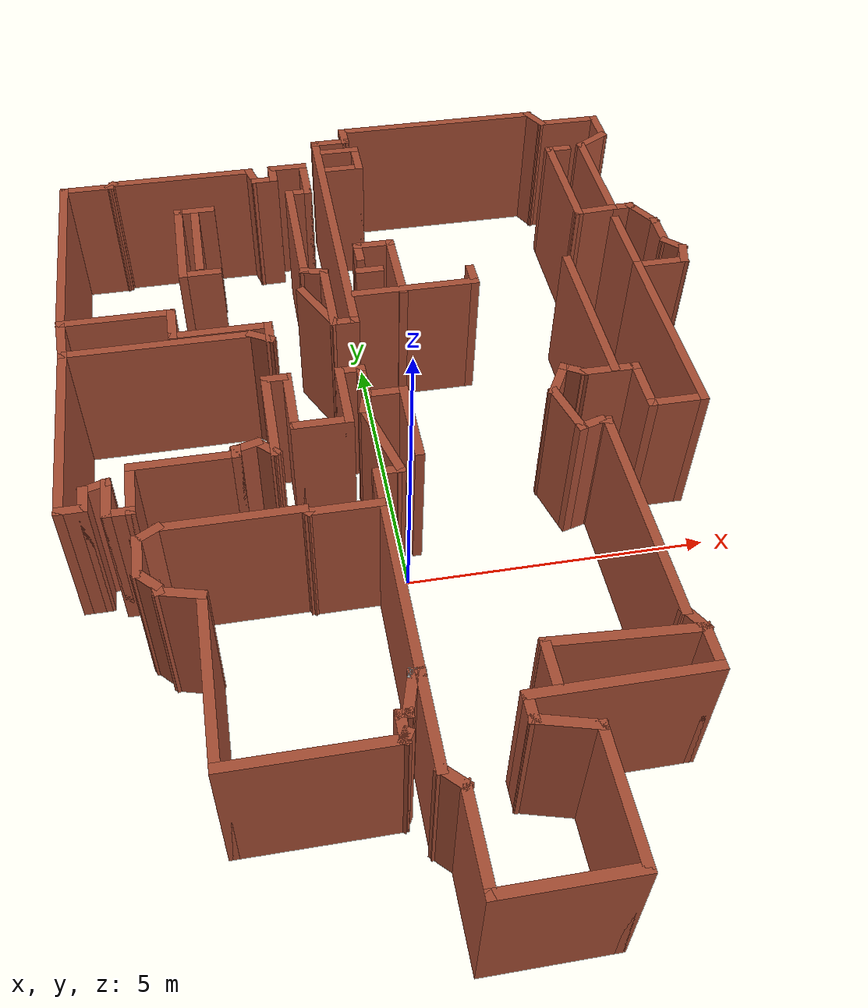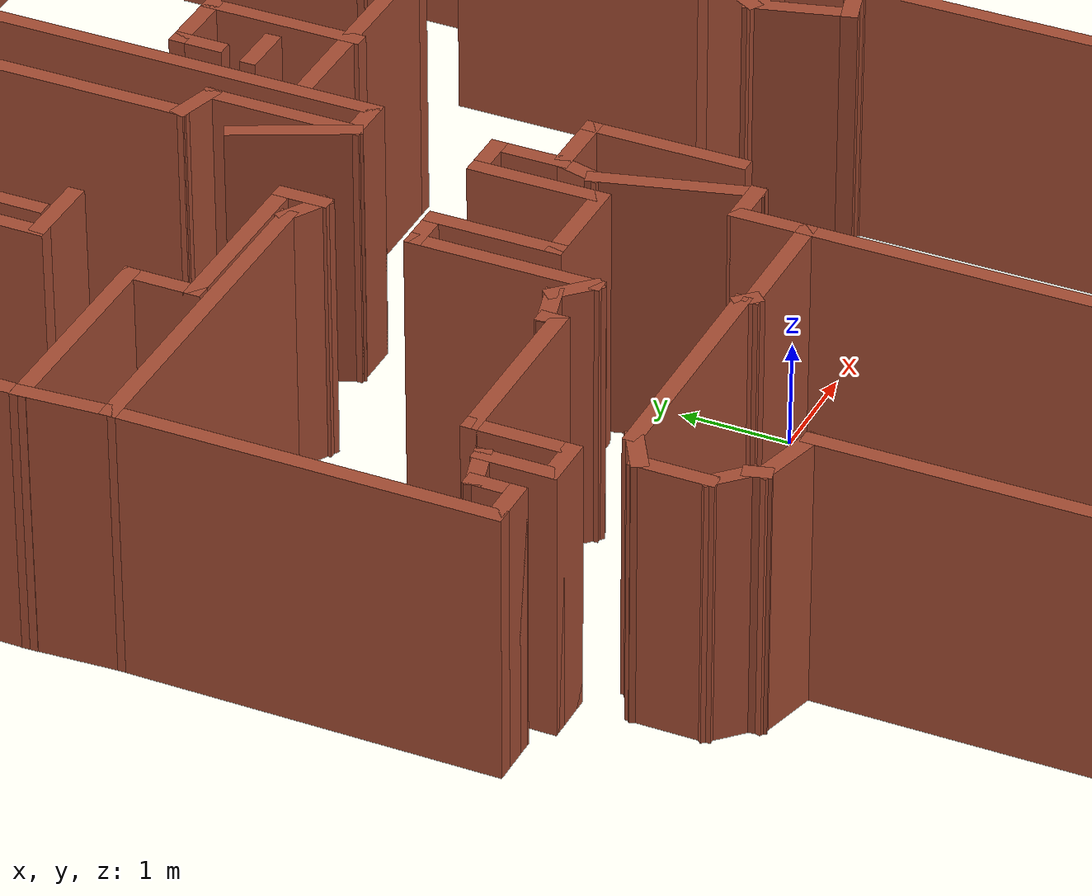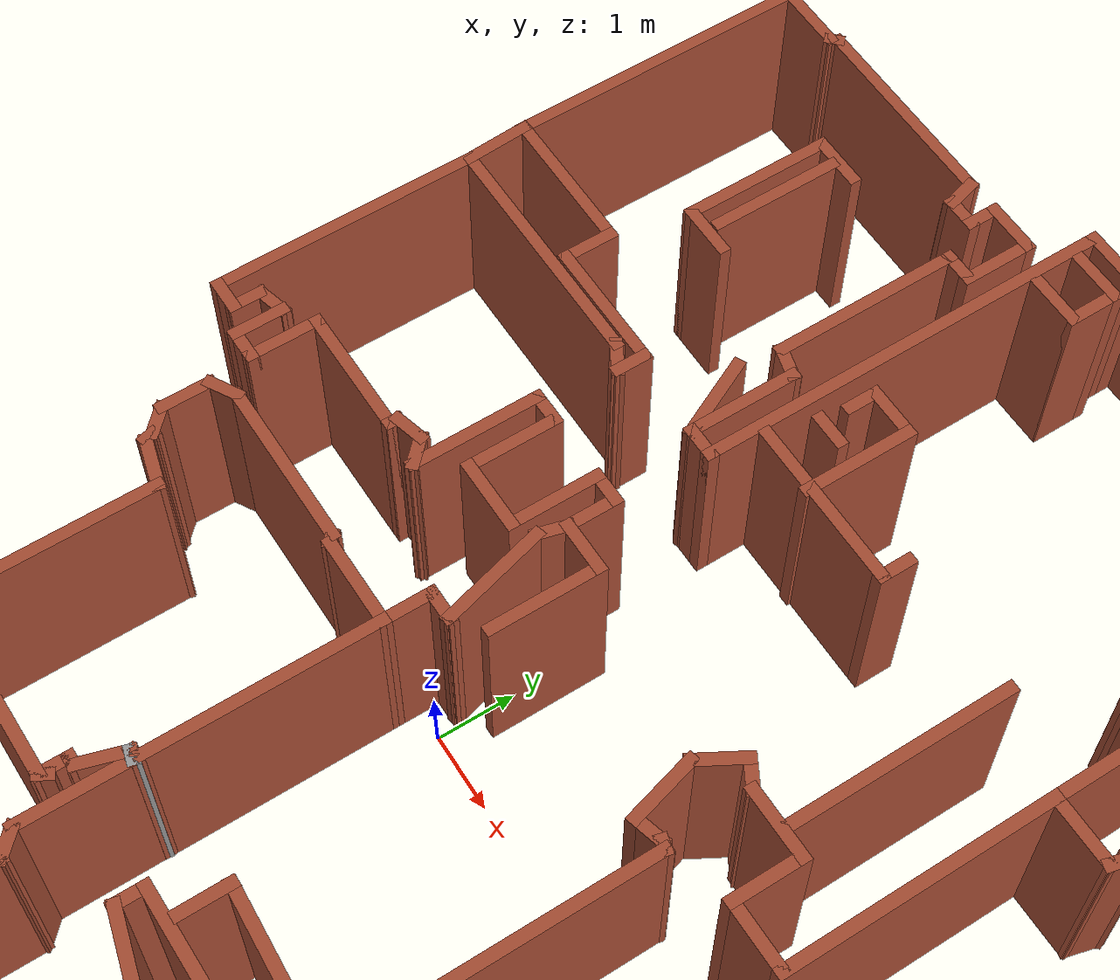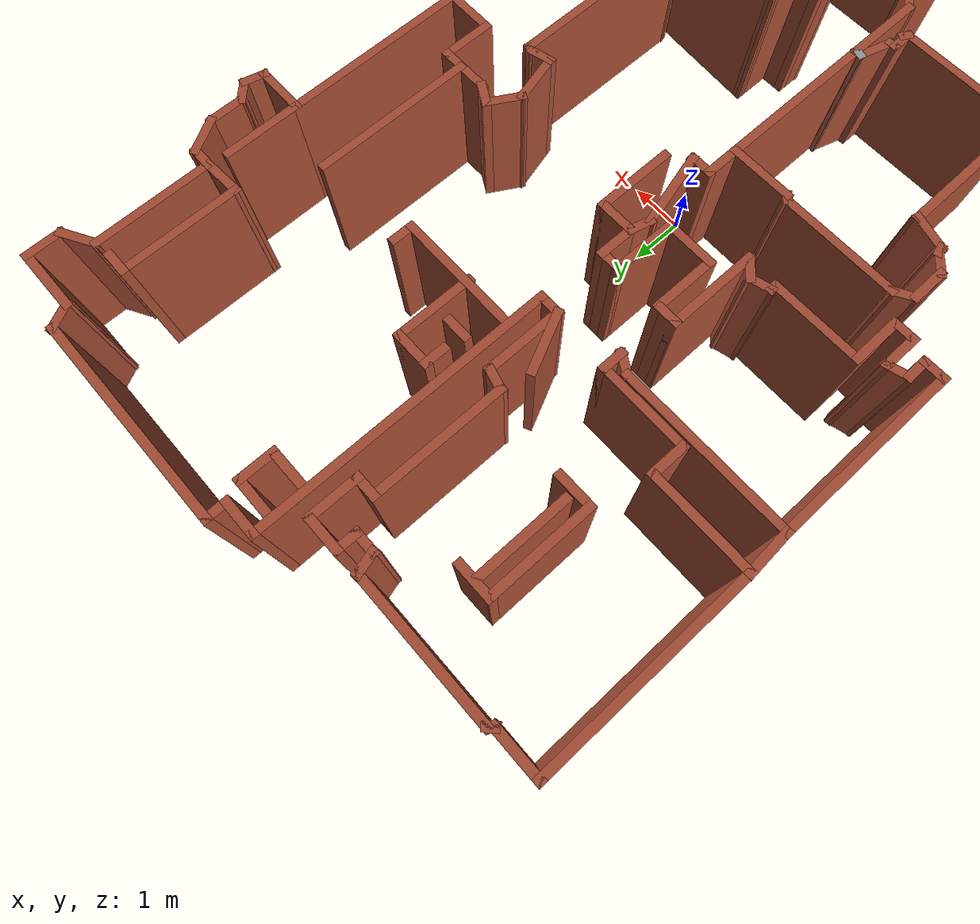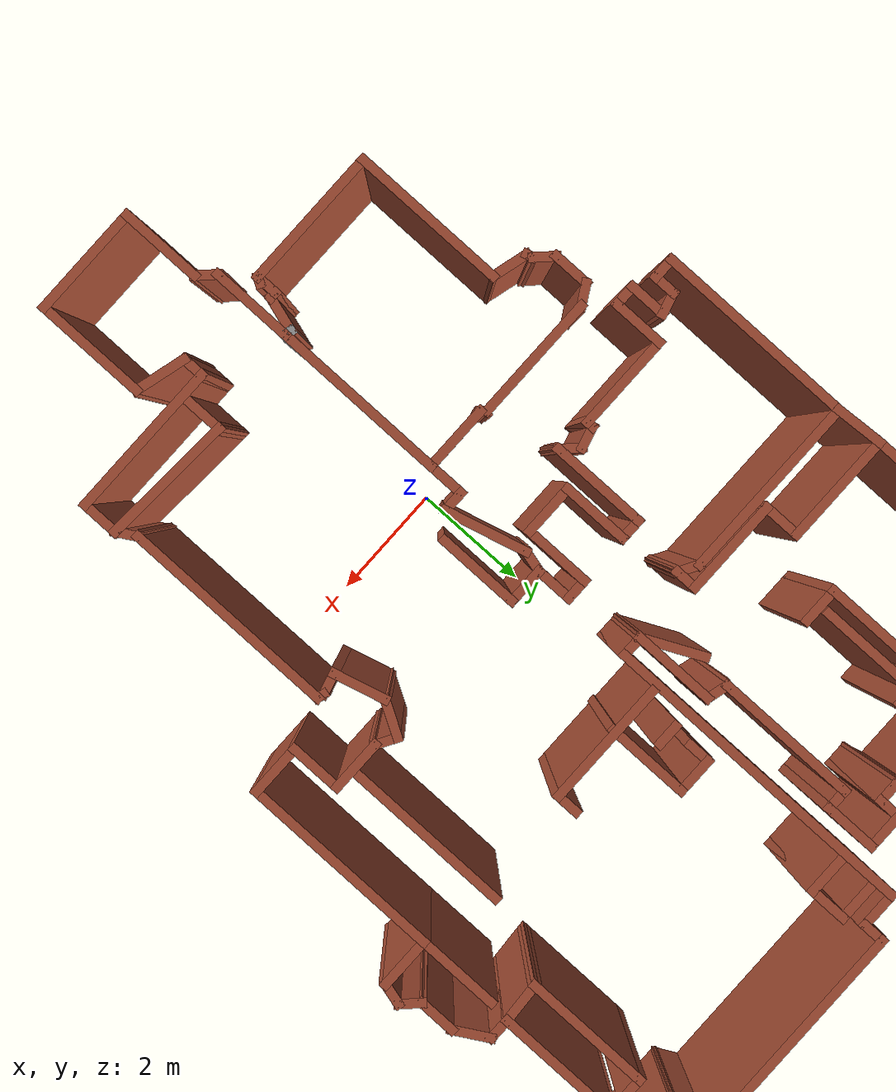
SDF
<?xml version='1.0'?>
<sdf version='1.6'>
  <model name='map_19'>
    <pose frame=''>0.347283 1.65481 0 0 -0 0</pose>
    <link name='Wall_0'>
      <collision name='Wall_0_Collision'>
        <geometry>
          <box>
            <size>4 0.15 2.5</size>
          </box>
        </geometry>
        <pose frame=''>0 0 1.25 0 -0 0</pose>
      </collision>
      <visual name='Wall_0_Visual'>
        <pose frame=''>0 0 1.25 0 -0 0</pose>
        <geometry>
          <box>
            <size>4 0.15 2.5</size>
          </box>
        </geometry>
        <material>
          <script>
            <uri>file://media/materials/scripts/gazebo.material</uri>
            <name>Gazebo/Bricks</name>
          </script>
          <ambient>1 1 1 1</ambient>
        </material>
        <meta>
          <layer>0</layer>
        </meta>
      </visual>
      <pose frame=''>1.90327 7.78441 0 0 -0 3.14159</pose>
    </link>
    <link name='Wall_1'>
      <collision name='Wall_1_Collision'>
        <geometry>
          <box>
            <size>0.5 0.15 2.5</size>
          </box>
        </geometry>
        <pose frame=''>0 0 1.25 0 -0 0</pose>
      </collision>
      <visual name='Wall_1_Visual'>
        <pose frame=''>0 0 1.25 0 -0 0</pose>
        <geometry>
          <box>
            <size>0.5 0.15 2.5</size>
          </box>
        </geometry>
        <material>
          <script>
            <uri>file://media/materials/scripts/gazebo.material</uri>
            <name>Gazebo/Bricks</name>
          </script>
          <ambient>1 1 1 1</ambient>
        </material>
        <meta>
          <layer>0</layer>
        </meta>
      </visual>
      <pose frame=''>-0.021727 7.60941 0 0 -0 -1.5708</pose>
    </link>
    <link name='Wall_100'>
      <collision name='Wall_100_Collision'>
        <geometry>
          <box>
            <size>0.25 0.15 2.5</size>
          </box>
        </geometry>
        <pose frame=''>0 0 1.25 0 -0 0</pose>
      </collision>
      <visual name='Wall_100_Visual'>
        <pose frame=''>0 0 1.25 0 -0 0</pose>
        <geometry>
          <box>
            <size>0.25 0.15 2.5</size>
          </box>
        </geometry>
        <material>
          <script>
            <uri>file://media/materials/scripts/gazebo.material</uri>
            <name>Gazebo/Grey</name>
          </script>
          <ambient>1 1 1 1</ambient>
        </material>
        <meta>
          <layer>0</layer>
        </meta>
      </visual>
      <pose frame=''>-0.844355 -4.84999 0 0 -0 -0.261799</pose>
    </link>
    <link name='Wall_101'>
      <collision name='Wall_101_Collision'>
        <geometry>
          <box>
            <size>1.5 0.15 2.5</size>
          </box>
        </geometry>
        <pose frame=''>0 0 1.25 0 -0 0</pose>
      </collision>
      <visual name='Wall_101_Visual'>
        <pose frame=''>0 0 1.25 0 -0 0</pose>
        <geometry>
          <box>
            <size>1.5 0.15 2.5</size>
          </box>
        </geometry>
        <material>
          <script>
            <uri>file://media/materials/scripts/gazebo.material</uri>
            <name>Gazebo/Bricks</name>
          </script>
          <ambient>1 1 1 1</ambient>
        </material>
        <meta>
          <layer>0</layer>
        </meta>
      </visual>
      <pose frame=''>-0.796059 -5.53794 0 0 -0 -1.5708</pose>
    </link>
    <link name='Wall_102'>
      <collision name='Wall_102_Collision'>
        <geometry>
          <box>
            <size>0.5 0.15 2.5</size>
          </box>
        </geometry>
        <pose frame=''>0 0 1.25 0 -0 0</pose>
      </collision>
      <visual name='Wall_102_Visual'>
        <pose frame=''>0 0 1.25 0 -0 0</pose>
        <geometry>
          <box>
            <size>0.5 0.15 2.5</size>
          </box>
        </geometry>
        <material>
          <script>
            <uri>file://media/materials/scripts/gazebo.material</uri>
            <name>Gazebo/Bricks</name>
          </script>
          <ambient>1 1 1 1</ambient>
        </material>
        <meta>
          <layer>0</layer>
        </meta>
      </visual>
      <pose frame=''>-0.672315 -6.33668 0 0 -0 -0.785398</pose>
    </link>
    <link name='Wall_103'>
      <collision name='Wall_103_Collision'>
        <geometry>
          <box>
            <size>1.5 0.15 2.5</size>
          </box>
        </geometry>
        <pose frame=''>0 0 1.25 0 -0 0</pose>
      </collision>
      <visual name='Wall_103_Visual'>
        <pose frame=''>0 0 1.25 0 -0 0</pose>
        <geometry>
          <box>
            <size>1.5 0.15 2.5</size>
          </box>
        </geometry>
        <material>
          <script>
            <uri>file://media/materials/scripts/gazebo.material</uri>
            <name>Gazebo/Bricks</name>
          </script>
          <ambient>1 1 1 1</ambient>
        </material>
        <meta>
          <layer>0</layer>
        </meta>
      </visual>
      <pose frame=''>-0.548571 -7.13542 0 0 -0 -1.5708</pose>
    </link>
    <link name='Wall_106'>
      <collision name='Wall_106_Collision'>
        <geometry>
          <box>
            <size>2 0.15 2.5</size>
          </box>
        </geometry>
        <pose frame=''>0 0 1.25 0 -0 0</pose>
      </collision>
      <visual name='Wall_106_Visual'>
        <pose frame=''>0 0 1.25 0 -0 0</pose>
        <geometry>
          <box>
            <size>2 0.15 2.5</size>
          </box>
        </geometry>
        <material>
          <script>
            <uri>file://media/materials/scripts/gazebo.material</uri>
            <name>Gazebo/Bricks</name>
          </script>
          <ambient>1 1 1 1</ambient>
        </material>
        <meta>
          <layer>0</layer>
        </meta>
      </visual>
      <pose frame=''>0.376429 -7.81042 0 0 -0 0</pose>
    </link>
    <link name='Wall_107'>
      <collision name='Wall_107_Collision'>
        <geometry>
          <box>
            <size>2 0.15 2.5</size>
          </box>
        </geometry>
        <pose frame=''>0 0 1.25 0 -0 0</pose>
      </collision>
      <visual name='Wall_107_Visual'>
        <pose frame=''>0 0 1.25 0 -0 0</pose>
        <geometry>
          <box>
            <size>2 0.15 2.5</size>
          </box>
        </geometry>
        <material>
          <script>
            <uri>file://media/materials/scripts/gazebo.material</uri>
            <name>Gazebo/Bricks</name>
          </script>
          <ambient>1 1 1 1</ambient>
        </material>
        <meta>
          <layer>0</layer>
        </meta>
      </visual>
      <pose frame=''>1.30143 -6.88542 0 0 -0 1.5708</pose>
    </link>
    <link name='Wall_108'>
      <collision name='Wall_108_Collision'>
        <geometry>
          <box>
            <size>1 0.15 2.5</size>
          </box>
        </geometry>
        <pose frame=''>0 0 1.25 0 -0 0</pose>
      </collision>
      <visual name='Wall_108_Visual'>
        <pose frame=''>0 0 1.25 0 -0 0</pose>
        <geometry>
          <box>
            <size>1 0.15 2.5</size>
          </box>
        </geometry>
        <material>
          <script>
            <uri>file://media/materials/scripts/gazebo.material</uri>
            <name>Gazebo/Bricks</name>
          </script>
          <ambient>1 1 1 1</ambient>
        </material>
        <meta>
          <layer>0</layer>
        </meta>
      </visual>
      <pose frame=''>0.89091 -5.85042 0 0 -0 2.87979</pose>
    </link>
    <link name='Wall_109'>
      <collision name='Wall_109_Collision'>
        <geometry>
          <box>
            <size>0.5 0.15 2.5</size>
          </box>
        </geometry>
        <pose frame=''>0 0 1.25 0 -0 0</pose>
      </collision>
      <visual name='Wall_109_Visual'>
        <pose frame=''>0 0 1.25 0 -0 0</pose>
        <geometry>
          <box>
            <size>0.5 0.15 2.5</size>
          </box>
        </geometry>
        <material>
          <script>
            <uri>file://media/materials/scripts/gazebo.material</uri>
            <name>Gazebo/Bricks</name>
          </script>
          <ambient>1 1 1 1</ambient>
        </material>
        <meta>
          <layer>0</layer>
        </meta>
      </visual>
      <pose frame=''>0.480392 -5.56543 0 0 -0 1.5708</pose>
    </link>
    <link name='Wall_11'>
      <collision name='Wall_11_Collision'>
        <geometry>
          <box>
            <size>1 0.15 2.5</size>
          </box>
        </geometry>
        <pose frame=''>0 0 1.25 0 -0 0</pose>
      </collision>
      <visual name='Wall_11_Visual'>
        <pose frame=''>0 0 1.25 0 -0 0</pose>
        <geometry>
          <box>
            <size>1 0.15 2.5</size>
          </box>
        </geometry>
        <material>
          <script>
            <uri>file://media/materials/scripts/gazebo.material</uri>
            <name>Gazebo/Bricks</name>
          </script>
          <ambient>1 1 1 1</ambient>
        </material>
        <meta>
          <layer>0</layer>
        </meta>
      </visual>
      <pose frame=''>-0.959801 6.29999 0 0 -0 1.5708</pose>
    </link>
    <link name='Wall_110'>
      <collision name='Wall_110_Collision'>
        <geometry>
          <box>
            <size>2.75 0.15 2.5</size>
          </box>
        </geometry>
        <pose frame=''>0 0 1.25 0 -0 0</pose>
      </collision>
      <visual name='Wall_110_Visual'>
        <pose frame=''>0 0 1.25 0 -0 0</pose>
        <geometry>
          <box>
            <size>2.75 0.15 2.5</size>
          </box>
        </geometry>
        <material>
          <script>
            <uri>file://media/materials/scripts/gazebo.material</uri>
            <name>Gazebo/Bricks</name>
          </script>
          <ambient>1 1 1 1</ambient>
        </material>
        <meta>
          <layer>0</layer>
        </meta>
      </visual>
      <pose frame=''>1.78039 -5.39043 0 0 -0 0</pose>
    </link>
    <link name='Wall_113'>
      <collision name='Wall_113_Collision'>
        <geometry>
          <box>
            <size>0.75 0.15 2.5</size>
          </box>
        </geometry>
        <pose frame=''>0 0 1.25 0 -0 0</pose>
      </collision>
      <visual name='Wall_113_Visual'>
        <pose frame=''>0 0 1.25 0 -0 0</pose>
        <geometry>
          <box>
            <size>0.75 0.15 2.5</size>
          </box>
        </geometry>
        <material>
          <script>
            <uri>file://media/materials/scripts/gazebo.material</uri>
            <name>Gazebo/Bricks</name>
          </script>
          <ambient>1 1 1 1</ambient>
        </material>
        <meta>
          <layer>0</layer>
        </meta>
      </visual>
      <pose frame=''>3.08039 -5.09043 0 0 -0 1.5708</pose>
    </link>
    <link name='Wall_114'>
      <collision name='Wall_114_Collision'>
        <geometry>
          <box>
            <size>0.5 0.15 2.5</size>
          </box>
        </geometry>
        <pose frame=''>0 0 1.25 0 -0 0</pose>
      </collision>
      <visual name='Wall_114_Visual'>
        <pose frame=''>0 0 1.25 0 -0 0</pose>
        <geometry>
          <box>
            <size>0.5 0.15 2.5</size>
          </box>
        </geometry>
        <material>
          <script>
            <uri>file://media/materials/scripts/gazebo.material</uri>
            <name>Gazebo/Bricks</name>
          </script>
          <ambient>1 1 1 1</ambient>
        </material>
        <meta>
          <layer>0</layer>
        </meta>
      </visual>
      <pose frame=''>2.99289 -4.63887 0 0 -0 2.0944</pose>
    </link>
    <link name='Wall_115'>
      <collision name='Wall_115_Collision'>
        <geometry>
          <box>
            <size>3.75 0.15 2.5</size>
          </box>
        </geometry>
        <pose frame=''>0 0 1.25 0 -0 0</pose>
      </collision>
      <visual name='Wall_115_Visual'>
        <pose frame=''>0 0 1.25 0 -0 0</pose>
        <geometry>
          <box>
            <size>3.75 0.15 2.5</size>
          </box>
        </geometry>
        <material>
          <script>
            <uri>file://media/materials/scripts/gazebo.material</uri>
            <name>Gazebo/Bricks</name>
          </script>
          <ambient>1 1 1 1</ambient>
        </material>
        <meta>
          <layer>0</layer>
        </meta>
      </visual>
      <pose frame=''>2.90539 -2.68732 0 0 -0 1.5708</pose>
    </link>
    <link name='Wall_116'>
      <collision name='Wall_116_Collision'>
        <geometry>
          <box>
            <size>0.25 0.15 2.5</size>
          </box>
        </geometry>
        <pose frame=''>0 0 1.25 0 -0 0</pose>
      </collision>
      <visual name='Wall_116_Visual'>
        <pose frame=''>0 0 1.25 0 -0 0</pose>
        <geometry>
          <box>
            <size>0.25 0.15 2.5</size>
          </box>
        </geometry>
        <material>
          <script>
            <uri>file://media/materials/scripts/gazebo.material</uri>
            <name>Gazebo/Bricks</name>
          </script>
          <ambient>1 1 1 1</ambient>
        </material>
        <meta>
          <layer>0</layer>
        </meta>
      </visual>
      <pose frame=''>2.8571 -0.874376 0 0 -0 2.87979</pose>
    </link>
    <link name='Wall_117'>
      <collision name='Wall_117_Collision'>
        <geometry>
          <box>
            <size>0.5 0.15 2.5</size>
          </box>
        </geometry>
        <pose frame=''>0 0 1.25 0 -0 0</pose>
      </collision>
      <visual name='Wall_117_Visual'>
        <pose frame=''>0 0 1.25 0 -0 0</pose>
        <geometry>
          <box>
            <size>0.5 0.15 2.5</size>
          </box>
        </geometry>
        <material>
          <script>
            <uri>file://media/materials/scripts/gazebo.material</uri>
            <name>Gazebo/Bricks</name>
          </script>
          <ambient>1 1 1 1</ambient>
        </material>
        <meta>
          <layer>0</layer>
        </meta>
      </visual>
      <pose frame=''>2.63976 -0.906728 0 0 -0 -2.87979</pose>
    </link>
    <link name='Wall_118'>
      <collision name='Wall_118_Collision'>
        <geometry>
          <box>
            <size>1 0.15 2.5</size>
          </box>
        </geometry>
        <pose frame=''>0 0 1.25 0 -0 0</pose>
      </collision>
      <visual name='Wall_118_Visual'>
        <pose frame=''>0 0 1.25 0 -0 0</pose>
        <geometry>
          <box>
            <size>1 0.15 2.5</size>
          </box>
        </geometry>
        <material>
          <script>
            <uri>file://media/materials/scripts/gazebo.material</uri>
            <name>Gazebo/Bricks</name>
          </script>
          <ambient>1 1 1 1</ambient>
        </material>
        <meta>
          <layer>0</layer>
        </meta>
      </visual>
      <pose frame=''>2.36073 -0.541503 0 0 -0 1.8326</pose>
    </link>
    <link name='Wall_119'>
      <collision name='Wall_119_Collision'>
        <geometry>
          <box>
            <size>0.75 0.15 2.5</size>
          </box>
        </geometry>
        <pose frame=''>0 0 1.25 0 -0 0</pose>
      </collision>
      <visual name='Wall_119_Visual'>
        <pose frame=''>0 0 1.25 0 -0 0</pose>
        <geometry>
          <box>
            <size>0.75 0.15 2.5</size>
          </box>
        </geometry>
        <material>
          <script>
            <uri>file://media/materials/scripts/gazebo.material</uri>
            <name>Gazebo/Bricks</name>
          </script>
          <ambient>1 1 1 1</ambient>
        </material>
        <meta>
          <layer>0</layer>
        </meta>
      </visual>
      <pose frame=''>2.40073 0.128823 0 0 -0 1.0472</pose>
    </link>
    <link name='Wall_12'>
      <collision name='Wall_12_Collision'>
        <geometry>
          <box>
            <size>0.75 0.15 2.5</size>
          </box>
        </geometry>
        <pose frame=''>0 0 1.25 0 -0 0</pose>
      </collision>
      <visual name='Wall_12_Visual'>
        <pose frame=''>0 0 1.25 0 -0 0</pose>
        <geometry>
          <box>
            <size>0.75 0.15 2.5</size>
          </box>
        </geometry>
        <material>
          <script>
            <uri>file://media/materials/scripts/gazebo.material</uri>
            <name>Gazebo/Bricks</name>
          </script>
          <ambient>1 1 1 1</ambient>
        </material>
        <meta>
          <layer>0</layer>
        </meta>
      </visual>
      <pose frame=''>-1.2598 6.72499 0 0 -0 3.14159</pose>
    </link>
    <link name='Wall_120'>
      <collision name='Wall_120_Collision'>
        <geometry>
          <box>
            <size>0.5 0.15 2.5</size>
          </box>
        </geometry>
        <pose frame=''>0 0 1.25 0 -0 0</pose>
      </collision>
      <visual name='Wall_120_Visual'>
        <pose frame=''>0 0 1.25 0 -0 0</pose>
        <geometry>
          <box>
            <size>0.5 0.15 2.5</size>
          </box>
        </geometry>
        <material>
          <script>
            <uri>file://media/materials/scripts/gazebo.material</uri>
            <name>Gazebo/Bricks</name>
          </script>
          <ambient>1 1 1 1</ambient>
        </material>
        <meta>
          <layer>0</layer>
        </meta>
      </visual>
      <pose frame=''>2.70228 0.301131 0 0 -0 -0.523599</pose>
    </link>
    <link name='Wall_123'>
      <collision name='Wall_123_Collision'>
        <geometry>
          <box>
            <size>1 0.15 2.5</size>
          </box>
        </geometry>
        <pose frame=''>0 0 1.25 0 -0 0</pose>
      </collision>
      <visual name='Wall_123_Visual'>
        <pose frame=''>0 0 1.25 0 -0 0</pose>
        <geometry>
          <box>
            <size>1 0.15 2.5</size>
          </box>
        </geometry>
        <material>
          <script>
            <uri>file://media/materials/scripts/gazebo.material</uri>
            <name>Gazebo/Bricks</name>
          </script>
          <ambient>1 1 1 1</ambient>
        </material>
        <meta>
          <layer>0</layer>
        </meta>
      </visual>
      <pose frame=''>3.27884 0.213631 0 0 -0 0</pose>
    </link>
    <link name='Wall_124'>
      <collision name='Wall_124_Collision'>
        <geometry>
          <box>
            <size>1 0.15 2.5</size>
          </box>
        </geometry>
        <pose frame=''>0 0 1.25 0 -0 0</pose>
      </collision>
      <visual name='Wall_124_Visual'>
        <pose frame=''>0 0 1.25 0 -0 0</pose>
        <geometry>
          <box>
            <size>1 0.15 2.5</size>
          </box>
        </geometry>
        <material>
          <script>
            <uri>file://media/materials/scripts/gazebo.material</uri>
            <name>Gazebo/Bricks</name>
          </script>
          <ambient>1 1 1 1</ambient>
        </material>
        <meta>
          <layer>0</layer>
        </meta>
      </visual>
      <pose frame=''>3.70384 -0.21137 0 0 -0 -1.5708</pose>
    </link>
    <link name='Wall_125'>
      <collision name='Wall_125_Collision'>
        <geometry>
          <box>
            <size>1 0.15 2.5</size>
          </box>
        </geometry>
        <pose frame=''>0 0 1.25 0 -0 0</pose>
      </collision>
      <visual name='Wall_125_Visual'>
        <pose frame=''>0 0 1.25 0 -0 0</pose>
        <geometry>
          <box>
            <size>1 0.15 2.5</size>
          </box>
        </geometry>
        <material>
          <script>
            <uri>file://media/materials/scripts/gazebo.material</uri>
            <name>Gazebo/Bricks</name>
          </script>
          <ambient>1 1 1 1</ambient>
        </material>
        <meta>
          <layer>0</layer>
        </meta>
      </visual>
      <pose frame=''>4.12884 -0.636369 0 0 -0 0</pose>
    </link>
    <link name='Wall_126'>
      <collision name='Wall_126_Collision'>
        <geometry>
          <box>
            <size>3.5 0.15 2.5</size>
          </box>
        </geometry>
        <pose frame=''>0 0 1.25 0 -0 0</pose>
      </collision>
      <visual name='Wall_126_Visual'>
        <pose frame=''>0 0 1.25 0 -0 0</pose>
        <geometry>
          <box>
            <size>3.5 0.15 2.5</size>
          </box>
        </geometry>
        <material>
          <script>
            <uri>file://media/materials/scripts/gazebo.material</uri>
            <name>Gazebo/Bricks</name>
          </script>
          <ambient>1 1 1 1</ambient>
        </material>
        <meta>
          <layer>0</layer>
        </meta>
      </visual>
      <pose frame=''>4.55384 1.03863 0 0 -0 1.5708</pose>
    </link>
    <link name='Wall_127'>
      <collision name='Wall_127_Collision'>
        <geometry>
          <box>
            <size>1 0.15 2.5</size>
          </box>
        </geometry>
        <pose frame=''>0 0 1.25 0 -0 0</pose>
      </collision>
      <visual name='Wall_127_Visual'>
        <pose frame=''>0 0 1.25 0 -0 0</pose>
        <geometry>
          <box>
            <size>1 0.15 2.5</size>
          </box>
        </geometry>
        <material>
          <script>
            <uri>file://media/materials/scripts/gazebo.material</uri>
            <name>Gazebo/Bricks</name>
          </script>
          <ambient>1 1 1 1</ambient>
        </material>
        <meta>
          <layer>0</layer>
        </meta>
      </visual>
      <pose frame=''>4.97884 2.71363 0 0 -0 0</pose>
    </link>
    <link name='Wall_128'>
      <collision name='Wall_128_Collision'>
        <geometry>
          <box>
            <size>0.5 0.15 2.5</size>
          </box>
        </geometry>
        <pose frame=''>0 0 1.25 0 -0 0</pose>
      </collision>
      <visual name='Wall_128_Visual'>
        <pose frame=''>0 0 1.25 0 -0 0</pose>
        <geometry>
          <box>
            <size>0.5 0.15 2.5</size>
          </box>
        </geometry>
        <material>
          <script>
            <uri>file://media/materials/scripts/gazebo.material</uri>
            <name>Gazebo/Bricks</name>
          </script>
          <ambient>1 1 1 1</ambient>
        </material>
        <meta>
          <layer>0</layer>
        </meta>
      </visual>
      <pose frame=''>5.44913 2.88267 0 0 -0 1.309</pose>
    </link>
    <link name='Wall_129'>
      <collision name='Wall_129_Collision'>
        <geometry>
          <box>
            <size>0.5 0.15 2.5</size>
          </box>
        </geometry>
        <pose frame=''>0 0 1.25 0 -0 0</pose>
      </collision>
      <visual name='Wall_129_Visual'>
        <pose frame=''>0 0 1.25 0 -0 0</pose>
        <geometry>
          <box>
            <size>0.5 0.15 2.5</size>
          </box>
        </geometry>
        <material>
          <script>
            <uri>file://media/materials/scripts/gazebo.material</uri>
            <name>Gazebo/Bricks</name>
          </script>
          <ambient>1 1 1 1</ambient>
        </material>
        <meta>
          <layer>0</layer>
        </meta>
      </visual>
      <pose frame=''>5.37068 3.17545 0 0 -0 2.35619</pose>
    </link>
    <link name='Wall_13'>
      <collision name='Wall_13_Collision'>
        <geometry>
          <box>
            <size>0.5 0.15 2.5</size>
          </box>
        </geometry>
        <pose frame=''>0 0 1.25 0 -0 0</pose>
      </collision>
      <visual name='Wall_13_Visual'>
        <pose frame=''>0 0 1.25 0 -0 0</pose>
        <geometry>
          <box>
            <size>0.5 0.15 2.5</size>
          </box>
        </geometry>
        <material>
          <script>
            <uri>file://media/materials/scripts/gazebo.material</uri>
            <name>Gazebo/Bricks</name>
          </script>
          <ambient>1 1 1 1</ambient>
        </material>
        <meta>
          <layer>0</layer>
        </meta>
      </visual>
      <pose frame=''>-1.5598 6.54999 0 0 -0 -1.5708</pose>
    </link>
    <link name='Wall_130'>
      <collision name='Wall_130_Collision'>
        <geometry>
          <box>
            <size>0.75 0.15 2.5</size>
          </box>
        </geometry>
        <pose frame=''>0 0 1.25 0 -0 0</pose>
      </collision>
      <visual name='Wall_130_Visual'>
        <pose frame=''>0 0 1.25 0 -0 0</pose>
        <geometry>
          <box>
            <size>0.75 0.15 2.5</size>
          </box>
        </geometry>
        <material>
          <script>
            <uri>file://media/materials/scripts/gazebo.material</uri>
            <name>Gazebo/Bricks</name>
          </script>
          <ambient>1 1 1 1</ambient>
        </material>
        <meta>
          <layer>0</layer>
        </meta>
      </visual>
      <pose frame=''>5.24694 3.59919 0 0 -0 1.5708</pose>
    </link>
    <link name='Wall_131'>
      <collision name='Wall_131_Collision'>
        <geometry>
          <box>
            <size>0.75 0.15 2.5</size>
          </box>
        </geometry>
        <pose frame=''>0 0 1.25 0 -0 0</pose>
      </collision>
      <visual name='Wall_131_Visual'>
        <pose frame=''>0 0 1.25 0 -0 0</pose>
        <geometry>
          <box>
            <size>0.75 0.15 2.5</size>
          </box>
        </geometry>
        <material>
          <script>
            <uri>file://media/materials/scripts/gazebo.material</uri>
            <name>Gazebo/Bricks</name>
          </script>
          <ambient>1 1 1 1</ambient>
        </material>
        <meta>
          <layer>0</layer>
        </meta>
      </visual>
      <pose frame=''>5.09694 4.159 0 0 -0 2.0944</pose>
    </link>
    <link name='Wall_132'>
      <collision name='Wall_132_Collision'>
        <geometry>
          <box>
            <size>0.5 0.15 2.5</size>
          </box>
        </geometry>
        <pose frame=''>0 0 1.25 0 -0 0</pose>
      </collision>
      <visual name='Wall_132_Visual'>
        <pose frame=''>0 0 1.25 0 -0 0</pose>
        <geometry>
          <box>
            <size>0.5 0.15 2.5</size>
          </box>
        </geometry>
        <material>
          <script>
            <uri>file://media/materials/scripts/gazebo.material</uri>
            <name>Gazebo/Bricks</name>
          </script>
          <ambient>1 1 1 1</ambient>
        </material>
        <meta>
          <layer>0</layer>
        </meta>
      </visual>
      <pose frame=''>4.77194 4.41881 0 0 -0 3.14159</pose>
    </link>
    <link name='Wall_133'>
      <collision name='Wall_133_Collision'>
        <geometry>
          <box>
            <size>2.25 0.15 2.5</size>
          </box>
        </geometry>
        <pose frame=''>0 0 1.25 0 -0 0</pose>
      </collision>
      <visual name='Wall_133_Visual'>
        <pose frame=''>0 0 1.25 0 -0 0</pose>
        <geometry>
          <box>
            <size>2.25 0.15 2.5</size>
          </box>
        </geometry>
        <material>
          <script>
            <uri>file://media/materials/scripts/gazebo.material</uri>
            <name>Gazebo/Bricks</name>
          </script>
          <ambient>1 1 1 1</ambient>
        </material>
        <meta>
          <layer>0</layer>
        </meta>
      </visual>
      <pose frame=''>4.59694 5.46881 0 0 -0 1.5708</pose>
    </link>
    <link name='Wall_134'>
      <collision name='Wall_134_Collision'>
        <geometry>
          <box>
            <size>0.75 0.15 2.5</size>
          </box>
        </geometry>
        <pose frame=''>0 0 1.25 0 -0 0</pose>
      </collision>
      <visual name='Wall_134_Visual'>
        <pose frame=''>0 0 1.25 0 -0 0</pose>
        <geometry>
          <box>
            <size>0.75 0.15 2.5</size>
          </box>
        </geometry>
        <material>
          <script>
            <uri>file://media/materials/scripts/gazebo.material</uri>
            <name>Gazebo/Bricks</name>
          </script>
          <ambient>1 1 1 1</ambient>
        </material>
        <meta>
          <layer>0</layer>
        </meta>
      </visual>
      <pose frame=''>4.85675 6.66881 0 0 -0 0.523599</pose>
    </link>
    <link name='Wall_135'>
      <collision name='Wall_135_Collision'>
        <geometry>
          <box>
            <size>0.75 0.15 2.5</size>
          </box>
        </geometry>
        <pose frame=''>0 0 1.25 0 -0 0</pose>
      </collision>
      <visual name='Wall_135_Visual'>
        <pose frame=''>0 0 1.25 0 -0 0</pose>
        <geometry>
          <box>
            <size>0.75 0.15 2.5</size>
          </box>
        </geometry>
        <material>
          <script>
            <uri>file://media/materials/scripts/gazebo.material</uri>
            <name>Gazebo/Bricks</name>
          </script>
          <ambient>1 1 1 1</ambient>
        </material>
        <meta>
          <layer>0</layer>
        </meta>
      </visual>
      <pose frame=''>5.11655 7.11881 0 0 -0 1.5708</pose>
    </link>
    <link name='Wall_136'>
      <collision name='Wall_136_Collision'>
        <geometry>
          <box>
            <size>1.25 0.15 2.5</size>
          </box>
        </geometry>
        <pose frame=''>0 0 1.25 0 -0 0</pose>
      </collision>
      <visual name='Wall_136_Visual'>
        <pose frame=''>0 0 1.25 0 -0 0</pose>
        <geometry>
          <box>
            <size>1.25 0.15 2.5</size>
          </box>
        </geometry>
        <material>
          <script>
            <uri>file://media/materials/scripts/gazebo.material</uri>
            <name>Gazebo/Bricks</name>
          </script>
          <ambient>1 1 1 1</ambient>
        </material>
        <meta>
          <layer>0</layer>
        </meta>
      </visual>
      <pose frame=''>4.56655 7.41881 0 0 -0 3.14159</pose>
    </link>
    <link name='Wall_137'>
      <collision name='Wall_137_Collision'>
        <geometry>
          <box>
            <size>0.561232 0.15 2.5</size>
          </box>
        </geometry>
        <pose frame=''>0 0 1.25 0 -0 0</pose>
      </collision>
      <visual name='Wall_137_Visual'>
        <pose frame=''>0 0 1.25 0 -0 0</pose>
        <geometry>
          <box>
            <size>0.561232 0.15 2.5</size>
          </box>
        </geometry>
        <material>
          <script>
            <uri>file://media/materials/scripts/gazebo.material</uri>
            <name>Gazebo/Bricks</name>
          </script>
          <ambient>1 1 1 1</ambient>
        </material>
        <meta>
          <layer>0</layer>
        </meta>
      </visual>
      <pose frame=''>3.92241 7.60161 0 0 -0 2.04636</pose>
    </link>
    <link name='Wall_139'>
      <collision name='Wall_139_Collision'>
        <geometry>
          <box>
            <size>0.5 0.15 2.5</size>
          </box>
        </geometry>
        <pose frame=''>0 0 1.25 0 -0 0</pose>
      </collision>
      <visual name='Wall_139_Visual'>
        <pose frame=''>0 0 1.25 0 -0 0</pose>
        <geometry>
          <box>
            <size>0.5 0.15 2.5</size>
          </box>
        </geometry>
        <material>
          <script>
            <uri>file://media/materials/scripts/gazebo.material</uri>
            <name>Gazebo/Bricks</name>
          </script>
          <ambient>1 1 1 1</ambient>
        </material>
        <meta>
          <layer>0</layer>
        </meta>
      </visual>
      <pose frame=''>4.10877 6.47784 0 0 -0 3.14159</pose>
    </link>
    <link name='Wall_14'>
      <collision name='Wall_14_Collision'>
        <geometry>
          <box>
            <size>0.5 0.15 2.5</size>
          </box>
        </geometry>
        <pose frame=''>0 0 1.25 0 -0 0</pose>
      </collision>
      <visual name='Wall_14_Visual'>
        <pose frame=''>0 0 1.25 0 -0 0</pose>
        <geometry>
          <box>
            <size>0.5 0.15 2.5</size>
          </box>
        </geometry>
        <material>
          <script>
            <uri>file://media/materials/scripts/gazebo.material</uri>
            <name>Gazebo/Bricks</name>
          </script>
          <ambient>1 1 1 1</ambient>
        </material>
        <meta>
          <layer>0</layer>
        </meta>
      </visual>
      <pose frame=''>-1.7348 6.37499 0 0 -0 3.14159</pose>
    </link>
    <link name='Wall_140'>
      <collision name='Wall_140_Collision'>
        <geometry>
          <box>
            <size>2.25 0.15 2.5</size>
          </box>
        </geometry>
        <pose frame=''>0 0 1.25 0 -0 0</pose>
      </collision>
      <visual name='Wall_140_Visual'>
        <pose frame=''>0 0 1.25 0 -0 0</pose>
        <geometry>
          <box>
            <size>2.25 0.15 2.5</size>
          </box>
        </geometry>
        <material>
          <script>
            <uri>file://media/materials/scripts/gazebo.material</uri>
            <name>Gazebo/Bricks</name>
          </script>
          <ambient>1 1 1 1</ambient>
        </material>
        <meta>
          <layer>0</layer>
        </meta>
      </visual>
      <pose frame=''>3.93377 5.42784 0 0 -0 -1.5708</pose>
    </link>
    <link name='Wall_141'>
      <collision name='Wall_141_Collision'>
        <geometry>
          <box>
            <size>0.814436 0.15 2.5</size>
          </box>
        </geometry>
        <pose frame=''>0 0 1.25 0 -0 0</pose>
      </collision>
      <visual name='Wall_141_Visual'>
        <pose frame=''>0 0 1.25 0 -0 0</pose>
        <geometry>
          <box>
            <size>0.814436 0.15 2.5</size>
          </box>
        </geometry>
        <material>
          <script>
            <uri>file://media/materials/scripts/gazebo.material</uri>
            <name>Gazebo/Bricks</name>
          </script>
          <ambient>1 1 1 1</ambient>
        </material>
        <meta>
          <layer>0</layer>
        </meta>
      </visual>
      <pose frame=''>4.26535 4.39832 0 0 -0 0.061703</pose>
    </link>
    <link name='Wall_143'>
      <collision name='Wall_143_Collision'>
        <geometry>
          <box>
            <size>2 0.15 2.5</size>
          </box>
        </geometry>
        <pose frame=''>0 0 1.25 0 -0 0</pose>
      </collision>
      <visual name='Wall_143_Visual'>
        <pose frame=''>0 0 1.25 0 -0 0</pose>
        <geometry>
          <box>
            <size>2 0.15 2.5</size>
          </box>
        </geometry>
        <material>
          <script>
            <uri>file://media/materials/scripts/gazebo.material</uri>
            <name>Gazebo/Bricks</name>
          </script>
          <ambient>1 1 1 1</ambient>
        </material>
        <meta>
          <layer>0</layer>
        </meta>
      </visual>
      <pose frame=''>-3.41973 4.68795 0 0 -0 -1.5708</pose>
    </link>
    <link name='Wall_144'>
      <collision name='Wall_144_Collision'>
        <geometry>
          <box>
            <size>0.75 0.15 2.5</size>
          </box>
        </geometry>
        <pose frame=''>0 0 1.25 0 -0 0</pose>
      </collision>
      <visual name='Wall_144_Visual'>
        <pose frame=''>0 0 1.25 0 -0 0</pose>
        <geometry>
          <box>
            <size>0.75 0.15 2.5</size>
          </box>
        </geometry>
        <material>
          <script>
            <uri>file://media/materials/scripts/gazebo.material</uri>
            <name>Gazebo/Bricks</name>
          </script>
          <ambient>1 1 1 1</ambient>
        </material>
        <meta>
          <layer>0</layer>
        </meta>
      </visual>
      <pose frame=''>-3.11973 3.76295 0 0 -0 0</pose>
    </link>
    <link name='Wall_148'>
      <collision name='Wall_148_Collision'>
        <geometry>
          <box>
            <size>0.75 0.15 2.5</size>
          </box>
        </geometry>
        <pose frame=''>0 0 1.25 0 -0 0</pose>
      </collision>
      <visual name='Wall_148_Visual'>
        <pose frame=''>0 0 1.25 0 -0 0</pose>
        <geometry>
          <box>
            <size>0.75 0.15 2.5</size>
          </box>
        </geometry>
        <material>
          <script>
            <uri>file://media/materials/scripts/gazebo.material</uri>
            <name>Gazebo/Bricks</name>
          </script>
          <ambient>1 1 1 1</ambient>
        </material>
        <meta>
          <layer>0</layer>
        </meta>
      </visual>
      <pose frame=''>-3.11973 5.61295 0 0 -0 0</pose>
    </link>
    <link name='Wall_15'>
      <collision name='Wall_15_Collision'>
        <geometry>
          <box>
            <size>0.5 0.15 2.5</size>
          </box>
        </geometry>
        <pose frame=''>0 0 1.25 0 -0 0</pose>
      </collision>
      <visual name='Wall_15_Visual'>
        <pose frame=''>0 0 1.25 0 -0 0</pose>
        <geometry>
          <box>
            <size>0.5 0.15 2.5</size>
          </box>
        </geometry>
        <material>
          <script>
            <uri>file://media/materials/scripts/gazebo.material</uri>
            <name>Gazebo/Bricks</name>
          </script>
          <ambient>1 1 1 1</ambient>
        </material>
        <meta>
          <layer>0</layer>
        </meta>
      </visual>
      <pose frame=''>-1.95509 6.54403 0 0 -0 1.8326</pose>
    </link>
    <link name='Wall_150'>
      <collision name='Wall_150_Collision'>
        <geometry>
          <box>
            <size>1.75 0.15 2.5</size>
          </box>
        </geometry>
        <pose frame=''>0 0 1.25 0 -0 0</pose>
      </collision>
      <visual name='Wall_150_Visual'>
        <pose frame=''>0 0 1.25 0 -0 0</pose>
        <geometry>
          <box>
            <size>1.75 0.15 2.5</size>
          </box>
        </geometry>
        <material>
          <script>
            <uri>file://media/materials/scripts/gazebo.material</uri>
            <name>Gazebo/Bricks</name>
          </script>
          <ambient>1 1 1 1</ambient>
        </material>
        <meta>
          <layer>0</layer>
        </meta>
      </visual>
      <pose frame=''>-3.11803 4.7325 0 0 -0 -1.5708</pose>
    </link>
    <link name='Wall_152'>
      <collision name='Wall_152_Collision'>
        <geometry>
          <box>
            <size>2.25 0.15 2.5</size>
          </box>
        </geometry>
        <pose frame=''>0 0 1.25 0 -0 0</pose>
      </collision>
      <visual name='Wall_152_Visual'>
        <pose frame=''>0 0 1.25 0 -0 0</pose>
        <geometry>
          <box>
            <size>2.25 0.15 2.5</size>
          </box>
        </geometry>
        <material>
          <script>
            <uri>file://media/materials/scripts/gazebo.material</uri>
            <name>Gazebo/Bricks</name>
          </script>
          <ambient>1 1 1 1</ambient>
        </material>
        <meta>
          <layer>0</layer>
        </meta>
      </visual>
      <pose frame=''>0.546736 2.75683 0 0 -0 0</pose>
    </link>
    <link name='Wall_153'>
      <collision name='Wall_153_Collision'>
        <geometry>
          <box>
            <size>0.5 0.15 2.5</size>
          </box>
        </geometry>
        <pose frame=''>0 0 1.25 0 -0 0</pose>
      </collision>
      <visual name='Wall_153_Visual'>
        <pose frame=''>0 0 1.25 0 -0 0</pose>
        <geometry>
          <box>
            <size>0.5 0.15 2.5</size>
          </box>
        </geometry>
        <material>
          <script>
            <uri>file://media/materials/scripts/gazebo.material</uri>
            <name>Gazebo/Bricks</name>
          </script>
          <ambient>1 1 1 1</ambient>
        </material>
        <meta>
          <layer>0</layer>
        </meta>
      </visual>
      <pose frame=''>1.59674 2.93182 0 0 -0 1.5708</pose>
    </link>
    <link name='Wall_155'>
      <collision name='Wall_155_Collision'>
        <geometry>
          <box>
            <size>0.75 0.15 2.5</size>
          </box>
        </geometry>
        <pose frame=''>0 0 1.25 0 -0 0</pose>
      </collision>
      <visual name='Wall_155_Visual'>
        <pose frame=''>0 0 1.25 0 -0 0</pose>
        <geometry>
          <box>
            <size>0.75 0.15 2.5</size>
          </box>
        </geometry>
        <material>
          <script>
            <uri>file://media/materials/scripts/gazebo.material</uri>
            <name>Gazebo/Bricks</name>
          </script>
          <ambient>1 1 1 1</ambient>
        </material>
        <meta>
          <layer>0</layer>
        </meta>
      </visual>
      <pose frame=''>0.017985 4.06421 0 0 -0 0</pose>
    </link>
    <link name='Wall_156'>
      <collision name='Wall_156_Collision'>
        <geometry>
          <box>
            <size>1.5 0.15 2.5</size>
          </box>
        </geometry>
        <pose frame=''>0 0 1.25 0 -0 0</pose>
      </collision>
      <visual name='Wall_156_Visual'>
        <pose frame=''>0 0 1.25 0 -0 0</pose>
        <geometry>
          <box>
            <size>1.5 0.15 2.5</size>
          </box>
        </geometry>
        <material>
          <script>
            <uri>file://media/materials/scripts/gazebo.material</uri>
            <name>Gazebo/Bricks</name>
          </script>
          <ambient>1 1 1 1</ambient>
        </material>
        <meta>
          <layer>0</layer>
        </meta>
      </visual>
      <pose frame=''>0.317985 3.38921 0 0 -0 -1.5708</pose>
    </link>
    <link name='Wall_158'>
      <collision name='Wall_158_Collision'>
        <geometry>
          <box>
            <size>0.5 0.15 2.5</size>
          </box>
        </geometry>
        <pose frame=''>0 0 1.25 0 -0 0</pose>
      </collision>
      <visual name='Wall_158_Visual'>
        <pose frame=''>0 0 1.25 0 -0 0</pose>
        <geometry>
          <box>
            <size>0.5 0.15 2.5</size>
          </box>
        </geometry>
        <material>
          <script>
            <uri>file://media/materials/scripts/gazebo.material</uri>
            <name>Gazebo/Bricks</name>
          </script>
          <ambient>1 1 1 1</ambient>
        </material>
        <meta>
          <layer>0</layer>
        </meta>
      </visual>
      <pose frame=''>-0.282015 3.88921 0 0 -0 -1.5708</pose>
    </link>
    <link name='Wall_16'>
      <collision name='Wall_16_Collision'>
        <geometry>
          <box>
            <size>2.75 0.15 2.5</size>
          </box>
        </geometry>
        <pose frame=''>0 0 1.25 0 -0 0</pose>
      </collision>
      <visual name='Wall_16_Visual'>
        <pose frame=''>0 0 1.25 0 -0 0</pose>
        <geometry>
          <box>
            <size>2.75 0.15 2.5</size>
          </box>
        </geometry>
        <material>
          <script>
            <uri>file://media/materials/scripts/gazebo.material</uri>
            <name>Gazebo/Bricks</name>
          </script>
          <ambient>1 1 1 1</ambient>
        </material>
        <meta>
          <layer>0</layer>
        </meta>
      </visual>
      <pose frame=''>-3.30039 6.71307 0 0 -0 3.14159</pose>
    </link>
    <link name='Wall_160'>
      <collision name='Wall_160_Collision'>
        <geometry>
          <box>
            <size>0.5 0.15 2.5</size>
          </box>
        </geometry>
        <pose frame=''>0 0 1.25 0 -0 0</pose>
      </collision>
      <visual name='Wall_160_Visual'>
        <pose frame=''>0 0 1.25 0 -0 0</pose>
        <geometry>
          <box>
            <size>0.5 0.15 2.5</size>
          </box>
        </geometry>
        <material>
          <script>
            <uri>file://media/materials/scripts/gazebo.material</uri>
            <name>Gazebo/Bricks</name>
          </script>
          <ambient>1 1 1 1</ambient>
        </material>
        <meta>
          <layer>0</layer>
        </meta>
      </visual>
      <pose frame=''>-0.167356 3.36023 0 0 -0 0</pose>
    </link>
    <link name='Wall_165'>
      <collision name='Wall_165_Collision'>
        <geometry>
          <box>
            <size>0.75 0.15 2.5</size>
          </box>
        </geometry>
        <pose frame=''>0 0 1.25 0 -0 0</pose>
      </collision>
      <visual name='Wall_165_Visual'>
        <pose frame=''>0 0 1.25 0 -0 0</pose>
        <geometry>
          <box>
            <size>0.75 0.15 2.5</size>
          </box>
        </geometry>
        <material>
          <script>
            <uri>file://media/materials/scripts/gazebo.material</uri>
            <name>Gazebo/Bricks</name>
          </script>
          <ambient>1 1 1 1</ambient>
        </material>
        <meta>
          <layer>0</layer>
        </meta>
      </visual>
      <pose frame=''>-0.183151 6.51806 0 0 -0 0</pose>
    </link>
    <link name='Wall_166'>
      <collision name='Wall_166_Collision'>
        <geometry>
          <box>
            <size>0.75 0.15 2.5</size>
          </box>
        </geometry>
        <pose frame=''>0 0 1.25 0 -0 0</pose>
      </collision>
      <visual name='Wall_166_Visual'>
        <pose frame=''>0 0 1.25 0 -0 0</pose>
        <geometry>
          <box>
            <size>0.75 0.15 2.5</size>
          </box>
        </geometry>
        <material>
          <script>
            <uri>file://media/materials/scripts/gazebo.material</uri>
            <name>Gazebo/Bricks</name>
          </script>
          <ambient>1 1 1 1</ambient>
        </material>
        <meta>
          <layer>0</layer>
        </meta>
      </visual>
      <pose frame=''>0.116849 6.81806 0 0 -0 1.5708</pose>
    </link>
    <link name='Wall_167'>
      <collision name='Wall_167_Collision'>
        <geometry>
          <box>
            <size>0.75 0.15 2.5</size>
          </box>
        </geometry>
        <pose frame=''>0 0 1.25 0 -0 0</pose>
      </collision>
      <visual name='Wall_167_Visual'>
        <pose frame=''>0 0 1.25 0 -0 0</pose>
        <geometry>
          <box>
            <size>0.75 0.15 2.5</size>
          </box>
        </geometry>
        <material>
          <script>
            <uri>file://media/materials/scripts/gazebo.material</uri>
            <name>Gazebo/Bricks</name>
          </script>
          <ambient>1 1 1 1</ambient>
        </material>
        <meta>
          <layer>0</layer>
        </meta>
      </visual>
      <pose frame=''>-0.183151 7.11806 0 0 -0 3.14159</pose>
    </link>
    <link name='Wall_169'>
      <collision name='Wall_169_Collision'>
        <geometry>
          <box>
            <size>1.16275 0.15 2.5</size>
          </box>
        </geometry>
        <pose frame=''>0 0 1.25 0 -0 0</pose>
      </collision>
      <visual name='Wall_169_Visual'>
        <pose frame=''>0 0 1.25 0 -0 0</pose>
        <geometry>
          <box>
            <size>1.16275 0.15 2.5</size>
          </box>
        </geometry>
        <material>
          <script>
            <uri>file://media/materials/scripts/gazebo.material</uri>
            <name>Gazebo/Bricks</name>
          </script>
          <ambient>1 1 1 1</ambient>
        </material>
        <meta>
          <layer>0</layer>
        </meta>
      </visual>
      <pose frame=''>-1.19005 2.5413 0 0 -0 -1.12503</pose>
    </link>
    <link name='Wall_172'>
      <collision name='Wall_172_Collision'>
        <geometry>
          <box>
            <size>3 0.15 2.5</size>
          </box>
        </geometry>
        <pose frame=''>0 0 1.25 0 -0 0</pose>
      </collision>
      <visual name='Wall_172_Visual'>
        <pose frame=''>0 0 1.25 0 -0 0</pose>
        <geometry>
          <box>
            <size>3 0.15 2.5</size>
          </box>
        </geometry>
        <material>
          <script>
            <uri>file://media/materials/scripts/gazebo.material</uri>
            <name>Gazebo/Bricks</name>
          </script>
          <ambient>1 1 1 1</ambient>
        </material>
        <meta>
          <layer>0</layer>
        </meta>
      </visual>
      <pose frame=''>3.35854 1.65364 0 0 -0 -1.5708</pose>
    </link>
    <link name='Wall_174'>
      <collision name='Wall_174_Collision'>
        <geometry>
          <box>
            <size>1.5 0.15 2.5</size>
          </box>
        </geometry>
        <pose frame=''>0 0 1.25 0 -0 0</pose>
      </collision>
      <visual name='Wall_174_Visual'>
        <pose frame=''>0 0 1.25 0 -0 0</pose>
        <geometry>
          <box>
            <size>1.5 0.15 2.5</size>
          </box>
        </geometry>
        <material>
          <script>
            <uri>file://media/materials/scripts/gazebo.material</uri>
            <name>Gazebo/Bricks</name>
          </script>
          <ambient>1 1 1 1</ambient>
        </material>
        <meta>
          <layer>0</layer>
        </meta>
      </visual>
      <pose frame=''>4.55384 3.38863 0 0 -0 1.5708</pose>
    </link>
    <link name='Wall_176'>
      <collision name='Wall_176_Collision'>
        <geometry>
          <box>
            <size>0.75 0.15 2.5</size>
          </box>
        </geometry>
        <pose frame=''>0 0 1.25 0 -0 0</pose>
      </collision>
      <visual name='Wall_176_Visual'>
        <pose frame=''>0 0 1.25 0 -0 0</pose>
        <geometry>
          <box>
            <size>0.75 0.15 2.5</size>
          </box>
        </geometry>
        <material>
          <script>
            <uri>file://media/materials/scripts/gazebo.material</uri>
            <name>Gazebo/Bricks</name>
          </script>
          <ambient>1 1 1 1</ambient>
        </material>
        <meta>
          <layer>0</layer>
        </meta>
      </visual>
      <pose frame=''>-0.400572 0.301042 0 0 -0 0</pose>
    </link>
    <link name='Wall_177'>
      <collision name='Wall_177_Collision'>
        <geometry>
          <box>
            <size>1.5 0.15 2.5</size>
          </box>
        </geometry>
        <pose frame=''>0 0 1.25 0 -0 0</pose>
      </collision>
      <visual name='Wall_177_Visual'>
        <pose frame=''>0 0 1.25 0 -0 0</pose>
        <geometry>
          <box>
            <size>1.5 0.15 2.5</size>
          </box>
        </geometry>
        <material>
          <script>
            <uri>file://media/materials/scripts/gazebo.material</uri>
            <name>Gazebo/Bricks</name>
          </script>
          <ambient>1 1 1 1</ambient>
        </material>
        <meta>
          <layer>0</layer>
        </meta>
      </visual>
      <pose frame=''>-0.100572 -0.373958 0 0 -0 -1.5708</pose>
    </link>
    <link name='Wall_179'>
      <collision name='Wall_179_Collision'>
        <geometry>
          <box>
            <size>0.75 0.15 2.5</size>
          </box>
        </geometry>
        <pose frame=''>0 0 1.25 0 -0 0</pose>
      </collision>
      <visual name='Wall_179_Visual'>
        <pose frame=''>0 0 1.25 0 -0 0</pose>
        <geometry>
          <box>
            <size>0.75 0.15 2.5</size>
          </box>
        </geometry>
        <material>
          <script>
            <uri>file://media/materials/scripts/gazebo.material</uri>
            <name>Gazebo/Bricks</name>
          </script>
          <ambient>1 1 1 1</ambient>
        </material>
        <meta>
          <layer>0</layer>
        </meta>
      </visual>
      <pose frame=''>0.904686 -4.96508 0 0 -0 -1.5708</pose>
    </link>
    <link name='Wall_182'>
      <collision name='Wall_182_Collision'>
        <geometry>
          <box>
            <size>2.32931 0.15 2.5</size>
          </box>
        </geometry>
        <pose frame=''>0 0 1.25 0 -0 0</pose>
      </collision>
      <visual name='Wall_182_Visual'>
        <pose frame=''>0 0 1.25 0 -0 0</pose>
        <geometry>
          <box>
            <size>2.32931 0.15 2.5</size>
          </box>
        </geometry>
        <material>
          <script>
            <uri>file://media/materials/scripts/gazebo.material</uri>
            <name>Gazebo/Bricks</name>
          </script>
          <ambient>1 1 1 1</ambient>
        </material>
        <meta>
          <layer>0</layer>
        </meta>
      </visual>
      <pose frame=''>1.99254 -4.72775 0 0 -0 -0.057547</pose>
    </link>
    <link name='Wall_184'>
      <collision name='Wall_184_Collision'>
        <geometry>
          <box>
            <size>3.07191 0.15 2.5</size>
          </box>
        </geometry>
        <pose frame=''>0 0 1.25 0 -0 0</pose>
      </collision>
      <visual name='Wall_184_Visual'>
        <pose frame=''>0 0 1.25 0 -0 0</pose>
        <geometry>
          <box>
            <size>3.07191 0.15 2.5</size>
          </box>
        </geometry>
        <material>
          <script>
            <uri>file://media/materials/scripts/gazebo.material</uri>
            <name>Gazebo/Bricks</name>
          </script>
          <ambient>1 1 1 1</ambient>
        </material>
        <meta>
          <layer>0</layer>
        </meta>
      </visual>
      <pose frame=''>-0.793906 -3.40198 0 0 -0 -1.57227</pose>
    </link>
    <link name='Wall_187'>
      <collision name='Wall_187_Collision'>
        <geometry>
          <box>
            <size>0.926417 0.15 2.5</size>
          </box>
        </geometry>
        <pose frame=''>0 0 1.25 0 -0 0</pose>
      </collision>
      <visual name='Wall_187_Visual'>
        <pose frame=''>0 0 1.25 0 -0 0</pose>
        <geometry>
          <box>
            <size>0.926417 0.15 2.5</size>
          </box>
        </geometry>
        <material>
          <script>
            <uri>file://media/materials/scripts/gazebo.material</uri>
            <name>Gazebo/Bricks</name>
          </script>
          <ambient>1 1 1 1</ambient>
        </material>
        <meta>
          <layer>0</layer>
        </meta>
      </visual>
      <pose frame=''>-5.49765 2.40486 0 0 -0 1.63123</pose>
    </link>
    <link name='Wall_2'>
      <collision name='Wall_2_Collision'>
        <geometry>
          <box>
            <size>0.75 0.15 2.5</size>
          </box>
        </geometry>
        <pose frame=''>0 0 1.25 0 -0 0</pose>
      </collision>
      <visual name='Wall_2_Visual'>
        <pose frame=''>0 0 1.25 0 -0 0</pose>
        <geometry>
          <box>
            <size>0.75 0.15 2.5</size>
          </box>
        </geometry>
        <material>
          <script>
            <uri>file://media/materials/scripts/gazebo.material</uri>
            <name>Gazebo/Bricks</name>
          </script>
          <ambient>1 1 1 1</ambient>
        </material>
        <meta>
          <layer>0</layer>
        </meta>
      </visual>
      <pose frame=''>-0.321727 7.43441 0 0 -0 3.14159</pose>
    </link>
    <link name='Wall_22'>
      <collision name='Wall_22_Collision'>
        <geometry>
          <box>
            <size>0.25 0.15 2.5</size>
          </box>
        </geometry>
        <pose frame=''>0 0 1.25 0 -0 0</pose>
      </collision>
      <visual name='Wall_22_Visual'>
        <pose frame=''>0 0 1.25 0 -0 0</pose>
        <geometry>
          <box>
            <size>0.25 0.15 2.5</size>
          </box>
        </geometry>
        <material>
          <script>
            <uri>file://media/materials/scripts/gazebo.material</uri>
            <name>Gazebo/Bricks</name>
          </script>
          <ambient>1 1 1 1</ambient>
        </material>
        <meta>
          <layer>0</layer>
        </meta>
      </visual>
      <pose frame=''>-4.63574 6.67771 0 0 -0 -2.35619</pose>
    </link>
    <link name='Wall_23'>
      <collision name='Wall_23_Collision'>
        <geometry>
          <box>
            <size>1 0.15 2.5</size>
          </box>
        </geometry>
        <pose frame=''>0 0 1.25 0 -0 0</pose>
      </collision>
      <visual name='Wall_23_Visual'>
        <pose frame=''>0 0 1.25 0 -0 0</pose>
        <geometry>
          <box>
            <size>1 0.15 2.5</size>
          </box>
        </geometry>
        <material>
          <script>
            <uri>file://media/materials/scripts/gazebo.material</uri>
            <name>Gazebo/Bricks</name>
          </script>
          <ambient>1 1 1 1</ambient>
        </material>
        <meta>
          <layer>0</layer>
        </meta>
      </visual>
      <pose frame=''>-5.0961 6.64236 0 0 -0 3.14159</pose>
    </link>
    <link name='Wall_24'>
      <collision name='Wall_24_Collision'>
        <geometry>
          <box>
            <size>4 0.15 2.5</size>
          </box>
        </geometry>
        <pose frame=''>0 0 1.25 0 -0 0</pose>
      </collision>
      <visual name='Wall_24_Visual'>
        <pose frame=''>0 0 1.25 0 -0 0</pose>
        <geometry>
          <box>
            <size>4 0.15 2.5</size>
          </box>
        </geometry>
        <material>
          <script>
            <uri>file://media/materials/scripts/gazebo.material</uri>
            <name>Gazebo/Bricks</name>
          </script>
          <ambient>1 1 1 1</ambient>
        </material>
        <meta>
          <layer>0</layer>
        </meta>
      </visual>
      <pose frame=''>-5.5211 4.71736 0 0 -0 -1.5708</pose>
    </link>
    <link name='Wall_27'>
      <collision name='Wall_27_Collision'>
        <geometry>
          <box>
            <size>2 0.15 2.5</size>
          </box>
        </geometry>
        <pose frame=''>0 0 1.25 0 -0 0</pose>
      </collision>
      <visual name='Wall_27_Visual'>
        <pose frame=''>0 0 1.25 0 -0 0</pose>
        <geometry>
          <box>
            <size>2 0.15 2.5</size>
          </box>
        </geometry>
        <material>
          <script>
            <uri>file://media/materials/scripts/gazebo.material</uri>
            <name>Gazebo/Bricks</name>
          </script>
          <ambient>1 1 1 1</ambient>
        </material>
        <meta>
          <layer>0</layer>
        </meta>
      </visual>
      <pose frame=''>-4.5961 2.79236 0 0 -0 0</pose>
    </link>
    <link name='Wall_3'>
      <collision name='Wall_3_Collision'>
        <geometry>
          <box>
            <size>5.5 0.15 2.5</size>
          </box>
        </geometry>
        <pose frame=''>0 0 1.25 0 -0 0</pose>
      </collision>
      <visual name='Wall_3_Visual'>
        <pose frame=''>0 0 1.25 0 -0 0</pose>
        <geometry>
          <box>
            <size>5.5 0.15 2.5</size>
          </box>
        </geometry>
        <material>
          <script>
            <uri>file://media/materials/scripts/gazebo.material</uri>
            <name>Gazebo/Bricks</name>
          </script>
          <ambient>1 1 1 1</ambient>
        </material>
        <meta>
          <layer>0</layer>
        </meta>
      </visual>
      <pose frame=''>-0.621727 4.75941 0 0 -0 -1.5708</pose>
    </link>
    <link name='Wall_30'>
      <collision name='Wall_30_Collision'>
        <geometry>
          <box>
            <size>0.75 0.15 2.5</size>
          </box>
        </geometry>
        <pose frame=''>0 0 1.25 0 -0 0</pose>
      </collision>
      <visual name='Wall_30_Visual'>
        <pose frame=''>0 0 1.25 0 -0 0</pose>
        <geometry>
          <box>
            <size>0.75 0.15 2.5</size>
          </box>
        </geometry>
        <material>
          <script>
            <uri>file://media/materials/scripts/gazebo.material</uri>
            <name>Gazebo/Bricks</name>
          </script>
          <ambient>1 1 1 1</ambient>
        </material>
        <meta>
          <layer>0</layer>
        </meta>
      </visual>
      <pose frame=''>-3.6711 2.49236 0 0 -0 -1.5708</pose>
    </link>
    <link name='Wall_31'>
      <collision name='Wall_31_Collision'>
        <geometry>
          <box>
            <size>1.75 0.15 2.5</size>
          </box>
        </geometry>
        <pose frame=''>0 0 1.25 0 -0 0</pose>
      </collision>
      <visual name='Wall_31_Visual'>
        <pose frame=''>0 0 1.25 0 -0 0</pose>
        <geometry>
          <box>
            <size>1.75 0.15 2.5</size>
          </box>
        </geometry>
        <material>
          <script>
            <uri>file://media/materials/scripts/gazebo.material</uri>
            <name>Gazebo/Bricks</name>
          </script>
          <ambient>1 1 1 1</ambient>
        </material>
        <meta>
          <layer>0</layer>
        </meta>
      </visual>
      <pose frame=''>-2.8711 2.19236 0 0 -0 0</pose>
    </link>
    <link name='Wall_32'>
      <collision name='Wall_32_Collision'>
        <geometry>
          <box>
            <size>0.5 0.15 2.5</size>
          </box>
        </geometry>
        <pose frame=''>0 0 1.25 0 -0 0</pose>
      </collision>
      <visual name='Wall_32_Visual'>
        <pose frame=''>0 0 1.25 0 -0 0</pose>
        <geometry>
          <box>
            <size>0.5 0.15 2.5</size>
          </box>
        </geometry>
        <material>
          <script>
            <uri>file://media/materials/scripts/gazebo.material</uri>
            <name>Gazebo/Bricks</name>
          </script>
          <ambient>1 1 1 1</ambient>
        </material>
        <meta>
          <layer>0</layer>
        </meta>
      </visual>
      <pose frame=''>-2.0711 2.01736 0 0 -0 -1.5708</pose>
    </link>
    <link name='Wall_33'>
      <collision name='Wall_33_Collision'>
        <geometry>
          <box>
            <size>0.5 0.15 2.5</size>
          </box>
        </geometry>
        <pose frame=''>0 0 1.25 0 -0 0</pose>
      </collision>
      <visual name='Wall_33_Visual'>
        <pose frame=''>0 0 1.25 0 -0 0</pose>
        <geometry>
          <box>
            <size>0.5 0.15 2.5</size>
          </box>
        </geometry>
        <material>
          <script>
            <uri>file://media/materials/scripts/gazebo.material</uri>
            <name>Gazebo/Bricks</name>
          </script>
          <ambient>1 1 1 1</ambient>
        </material>
        <meta>
          <layer>0</layer>
        </meta>
      </visual>
      <pose frame=''>-2.22265 1.92986 0 0 -0 2.61799</pose>
    </link>
    <link name='Wall_34'>
      <collision name='Wall_34_Collision'>
        <geometry>
          <box>
            <size>3.25 0.15 2.5</size>
          </box>
        </geometry>
        <pose frame=''>0 0 1.25 0 -0 0</pose>
      </collision>
      <visual name='Wall_34_Visual'>
        <pose frame=''>0 0 1.25 0 -0 0</pose>
        <geometry>
          <box>
            <size>3.25 0.15 2.5</size>
          </box>
        </geometry>
        <material>
          <script>
            <uri>file://media/materials/scripts/gazebo.material</uri>
            <name>Gazebo/Bricks</name>
          </script>
          <ambient>1 1 1 1</ambient>
        </material>
        <meta>
          <layer>0</layer>
        </meta>
      </visual>
      <pose frame=''>-3.92421 2.01736 0 0 -0 3.14159</pose>
    </link>
    <link name='Wall_35'>
      <collision name='Wall_35_Collision'>
        <geometry>
          <box>
            <size>3.5 0.15 2.5</size>
          </box>
        </geometry>
        <pose frame=''>0 0 1.25 0 -0 0</pose>
      </collision>
      <visual name='Wall_35_Visual'>
        <pose frame=''>0 0 1.25 0 -0 0</pose>
        <geometry>
          <box>
            <size>3.5 0.15 2.5</size>
          </box>
        </geometry>
        <material>
          <script>
            <uri>file://media/materials/scripts/gazebo.material</uri>
            <name>Gazebo/Bricks</name>
          </script>
          <ambient>1 1 1 1</ambient>
        </material>
        <meta>
          <layer>0</layer>
        </meta>
      </visual>
      <pose frame=''>-5.47421 0.342356 0 0 -0 -1.5708</pose>
    </link>
    <link name='Wall_36'>
      <collision name='Wall_36_Collision'>
        <geometry>
          <box>
            <size>0.5 0.15 2.5</size>
          </box>
        </geometry>
        <pose frame=''>0 0 1.25 0 -0 0</pose>
      </collision>
      <visual name='Wall_36_Visual'>
        <pose frame=''>0 0 1.25 0 -0 0</pose>
        <geometry>
          <box>
            <size>0.5 0.15 2.5</size>
          </box>
        </geometry>
        <material>
          <script>
            <uri>file://media/materials/scripts/gazebo.material</uri>
            <name>Gazebo/Bricks</name>
          </script>
          <ambient>1 1 1 1</ambient>
        </material>
        <meta>
          <layer>0</layer>
        </meta>
      </visual>
      <pose frame=''>-5.29921 -1.33264 0 0 -0 0</pose>
    </link>
    <link name='Wall_37'>
      <collision name='Wall_37_Collision'>
        <geometry>
          <box>
            <size>0.5 0.15 2.5</size>
          </box>
        </geometry>
        <pose frame=''>0 0 1.25 0 -0 0</pose>
      </collision>
      <visual name='Wall_37_Visual'>
        <pose frame=''>0 0 1.25 0 -0 0</pose>
        <geometry>
          <box>
            <size>0.5 0.15 2.5</size>
          </box>
        </geometry>
        <material>
          <script>
            <uri>file://media/materials/scripts/gazebo.material</uri>
            <name>Gazebo/Bricks</name>
          </script>
          <ambient>1 1 1 1</ambient>
        </material>
        <meta>
          <layer>0</layer>
        </meta>
      </visual>
      <pose frame=''>-5.12421 -1.15764 0 0 -0 1.5708</pose>
    </link>
    <link name='Wall_4'>
      <collision name='Wall_4_Collision'>
        <geometry>
          <box>
            <size>0.5 0.15 2.5</size>
          </box>
        </geometry>
        <pose frame=''>0 0 1.25 0 -0 0</pose>
      </collision>
      <visual name='Wall_4_Visual'>
        <pose frame=''>0 0 1.25 0 -0 0</pose>
        <geometry>
          <box>
            <size>0.5 0.15 2.5</size>
          </box>
        </geometry>
        <material>
          <script>
            <uri>file://media/materials/scripts/gazebo.material</uri>
            <name>Gazebo/Bricks</name>
          </script>
          <ambient>1 1 1 1</ambient>
        </material>
        <meta>
          <layer>0</layer>
        </meta>
      </visual>
      <pose frame=''>-0.796727 2.08441 0 0 -0 3.14159</pose>
    </link>
    <link name='Wall_42'>
      <collision name='Wall_42_Collision'>
        <geometry>
          <box>
            <size>0.5 0.15 2.5</size>
          </box>
        </geometry>
        <pose frame=''>0 0 1.25 0 -0 0</pose>
      </collision>
      <visual name='Wall_42_Visual'>
        <pose frame=''>0 0 1.25 0 -0 0</pose>
        <geometry>
          <box>
            <size>0.5 0.15 2.5</size>
          </box>
        </geometry>
        <material>
          <script>
            <uri>file://media/materials/scripts/gazebo.material</uri>
            <name>Gazebo/Bricks</name>
          </script>
          <ambient>1 1 1 1</ambient>
        </material>
        <meta>
          <layer>0</layer>
        </meta>
      </visual>
      <pose frame=''>-4.95517 -0.93735 0 0 -0 0.261799</pose>
    </link>
    <link name='Wall_43'>
      <collision name='Wall_43_Collision'>
        <geometry>
          <box>
            <size>0.75 0.15 2.5</size>
          </box>
        </geometry>
        <pose frame=''>0 0 1.25 0 -0 0</pose>
      </collision>
      <visual name='Wall_43_Visual'>
        <pose frame=''>0 0 1.25 0 -0 0</pose>
        <geometry>
          <box>
            <size>0.75 0.15 2.5</size>
          </box>
        </geometry>
        <material>
          <script>
            <uri>file://media/materials/scripts/gazebo.material</uri>
            <name>Gazebo/Bricks</name>
          </script>
          <ambient>1 1 1 1</ambient>
        </material>
        <meta>
          <layer>0</layer>
        </meta>
      </visual>
      <pose frame=''>-4.78613 -1.19206 0 0 -0 -1.5708</pose>
    </link>
    <link name='Wall_44'>
      <collision name='Wall_44_Collision'>
        <geometry>
          <box>
            <size>0.5 0.15 2.5</size>
          </box>
        </geometry>
        <pose frame=''>0 0 1.25 0 -0 0</pose>
      </collision>
      <visual name='Wall_44_Visual'>
        <pose frame=''>0 0 1.25 0 -0 0</pose>
        <geometry>
          <box>
            <size>0.5 0.15 2.5</size>
          </box>
        </geometry>
        <material>
          <script>
            <uri>file://media/materials/scripts/gazebo.material</uri>
            <name>Gazebo/Bricks</name>
          </script>
          <ambient>1 1 1 1</ambient>
        </material>
        <meta>
          <layer>0</layer>
        </meta>
      </visual>
      <pose frame=''>-4.61113 -1.49206 0 0 -0 0</pose>
    </link>
    <link name='Wall_45'>
      <collision name='Wall_45_Collision'>
        <geometry>
          <box>
            <size>1 0.15 2.5</size>
          </box>
        </geometry>
        <pose frame=''>0 0 1.25 0 -0 0</pose>
      </collision>
      <visual name='Wall_45_Visual'>
        <pose frame=''>0 0 1.25 0 -0 0</pose>
        <geometry>
          <box>
            <size>1 0.15 2.5</size>
          </box>
        </geometry>
        <material>
          <script>
            <uri>file://media/materials/scripts/gazebo.material</uri>
            <name>Gazebo/Bricks</name>
          </script>
          <ambient>1 1 1 1</ambient>
        </material>
        <meta>
          <layer>0</layer>
        </meta>
      </visual>
      <pose frame=''>-4.43613 -1.06706 0 0 -0 1.5708</pose>
    </link>
    <link name='Wall_5'>
      <collision name='Wall_5_Collision'>
        <geometry>
          <box>
            <size>1.5 0.15 2.5</size>
          </box>
        </geometry>
        <pose frame=''>0 0 1.25 0 -0 0</pose>
      </collision>
      <visual name='Wall_5_Visual'>
        <pose frame=''>0 0 1.25 0 -0 0</pose>
        <geometry>
          <box>
            <size>1.5 0.15 2.5</size>
          </box>
        </geometry>
        <material>
          <script>
            <uri>file://media/materials/scripts/gazebo.material</uri>
            <name>Gazebo/Bricks</name>
          </script>
          <ambient>1 1 1 1</ambient>
        </material>
        <meta>
          <layer>0</layer>
        </meta>
      </visual>
      <pose frame=''>-0.971727 2.75941 0 0 -0 1.5708</pose>
    </link>
    <link name='Wall_52'>
      <collision name='Wall_52_Collision'>
        <geometry>
          <box>
            <size>1.75 0.15 2.5</size>
          </box>
        </geometry>
        <pose frame=''>0 0 1.25 0 -0 0</pose>
      </collision>
      <visual name='Wall_52_Visual'>
        <pose frame=''>0 0 1.25 0 -0 0</pose>
        <geometry>
          <box>
            <size>1.75 0.15 2.5</size>
          </box>
        </geometry>
        <material>
          <script>
            <uri>file://media/materials/scripts/gazebo.material</uri>
            <name>Gazebo/Bricks</name>
          </script>
          <ambient>1 1 1 1</ambient>
        </material>
        <meta>
          <layer>0</layer>
        </meta>
      </visual>
      <pose frame=''>-3.63613 -0.642057 0 0 -0 0</pose>
    </link>
    <link name='Wall_53'>
      <collision name='Wall_53_Collision'>
        <geometry>
          <box>
            <size>0.25 0.15 2.5</size>
          </box>
        </geometry>
        <pose frame=''>0 0 1.25 0 -0 0</pose>
      </collision>
      <visual name='Wall_53_Visual'>
        <pose frame=''>0 0 1.25 0 -0 0</pose>
        <geometry>
          <box>
            <size>0.25 0.15 2.5</size>
          </box>
        </geometry>
        <material>
          <script>
            <uri>file://media/materials/scripts/gazebo.material</uri>
            <name>Gazebo/Bricks</name>
          </script>
          <ambient>1 1 1 1</ambient>
        </material>
        <meta>
          <layer>0</layer>
        </meta>
      </visual>
      <pose frame=''>-2.83613 -0.592057 0 0 -0 1.5708</pose>
    </link>
    <link name='Wall_54'>
      <collision name='Wall_54_Collision'>
        <geometry>
          <box>
            <size>0.5 0.15 2.5</size>
          </box>
        </geometry>
        <pose frame=''>0 0 1.25 0 -0 0</pose>
      </collision>
      <visual name='Wall_54_Visual'>
        <pose frame=''>0 0 1.25 0 -0 0</pose>
        <geometry>
          <box>
            <size>0.5 0.15 2.5</size>
          </box>
        </geometry>
        <material>
          <script>
            <uri>file://media/materials/scripts/gazebo.material</uri>
            <name>Gazebo/Bricks</name>
          </script>
          <ambient>1 1 1 1</ambient>
        </material>
        <meta>
          <layer>0</layer>
        </meta>
      </visual>
      <pose frame=''>-2.6671 -0.496764 0 0 -0 0.261799</pose>
    </link>
    <link name='Wall_55'>
      <collision name='Wall_55_Collision'>
        <geometry>
          <box>
            <size>0.5 0.15 2.5</size>
          </box>
        </geometry>
        <pose frame=''>0 0 1.25 0 -0 0</pose>
      </collision>
      <visual name='Wall_55_Visual'>
        <pose frame=''>0 0 1.25 0 -0 0</pose>
        <geometry>
          <box>
            <size>0.5 0.15 2.5</size>
          </box>
        </geometry>
        <material>
          <script>
            <uri>file://media/materials/scripts/gazebo.material</uri>
            <name>Gazebo/Bricks</name>
          </script>
          <ambient>1 1 1 1</ambient>
        </material>
        <meta>
          <layer>0</layer>
        </meta>
      </visual>
      <pose frame=''>-2.37432 -0.575214 0 0 -0 -0.785398</pose>
    </link>
    <link name='Wall_56'>
      <collision name='Wall_56_Collision'>
        <geometry>
          <box>
            <size>1.75 0.15 2.5</size>
          </box>
        </geometry>
        <pose frame=''>0 0 1.25 0 -0 0</pose>
      </collision>
      <visual name='Wall_56_Visual'>
        <pose frame=''>0 0 1.25 0 -0 0</pose>
        <geometry>
          <box>
            <size>1.75 0.15 2.5</size>
          </box>
        </geometry>
        <material>
          <script>
            <uri>file://media/materials/scripts/gazebo.material</uri>
            <name>Gazebo/Bricks</name>
          </script>
          <ambient>1 1 1 1</ambient>
        </material>
        <meta>
          <layer>0</layer>
        </meta>
      </visual>
      <pose frame=''>-2.25057 0.101042 0 0 -0 1.5708</pose>
    </link>
    <link name='Wall_57'>
      <collision name='Wall_57_Collision'>
        <geometry>
          <box>
            <size>0.5 0.15 2.5</size>
          </box>
        </geometry>
        <pose frame=''>0 0 1.25 0 -0 0</pose>
      </collision>
      <visual name='Wall_57_Visual'>
        <pose frame=''>0 0 1.25 0 -0 0</pose>
        <geometry>
          <box>
            <size>0.5 0.15 2.5</size>
          </box>
        </geometry>
        <material>
          <script>
            <uri>file://media/materials/scripts/gazebo.material</uri>
            <name>Gazebo/Bricks</name>
          </script>
          <ambient>1 1 1 1</ambient>
        </material>
        <meta>
          <layer>0</layer>
        </meta>
      </visual>
      <pose frame=''>-2.07557 0.901042 0 0 -0 0</pose>
    </link>
    <link name='Wall_58'>
      <collision name='Wall_58_Collision'>
        <geometry>
          <box>
            <size>1.25 0.15 2.5</size>
          </box>
        </geometry>
        <pose frame=''>0 0 1.25 0 -0 0</pose>
      </collision>
      <visual name='Wall_58_Visual'>
        <pose frame=''>0 0 1.25 0 -0 0</pose>
        <geometry>
          <box>
            <size>1.25 0.15 2.5</size>
          </box>
        </geometry>
        <material>
          <script>
            <uri>file://media/materials/scripts/gazebo.material</uri>
            <name>Gazebo/Bricks</name>
          </script>
          <ambient>1 1 1 1</ambient>
        </material>
        <meta>
          <layer>0</layer>
        </meta>
      </visual>
      <pose frame=''>-1.90057 0.351043 0 0 -0 -1.5708</pose>
    </link>
    <link name='Wall_59'>
      <collision name='Wall_59_Collision'>
        <geometry>
          <box>
            <size>1 0.15 2.5</size>
          </box>
        </geometry>
        <pose frame=''>0 0 1.25 0 -0 0</pose>
      </collision>
      <visual name='Wall_59_Visual'>
        <pose frame=''>0 0 1.25 0 -0 0</pose>
        <geometry>
          <box>
            <size>1 0.15 2.5</size>
          </box>
        </geometry>
        <material>
          <script>
            <uri>file://media/materials/scripts/gazebo.material</uri>
            <name>Gazebo/Bricks</name>
          </script>
          <ambient>1 1 1 1</ambient>
        </material>
        <meta>
          <layer>0</layer>
        </meta>
      </visual>
      <pose frame=''>-1.47557 -0.198958 0 0 -0 0</pose>
    </link>
    <link name='Wall_6'>
      <collision name='Wall_6_Collision'>
        <geometry>
          <box>
            <size>0.5 0.15 2.5</size>
          </box>
        </geometry>
        <pose frame=''>0 0 1.25 0 -0 0</pose>
      </collision>
      <visual name='Wall_6_Visual'>
        <pose frame=''>0 0 1.25 0 -0 0</pose>
        <geometry>
          <box>
            <size>0.5 0.15 2.5</size>
          </box>
        </geometry>
        <material>
          <script>
            <uri>file://media/materials/scripts/gazebo.material</uri>
            <name>Gazebo/Bricks</name>
          </script>
          <ambient>1 1 1 1</ambient>
        </material>
        <meta>
          <layer>0</layer>
        </meta>
      </visual>
      <pose frame=''>-1.14076 3.4797 0 0 -0 2.87979</pose>
    </link>
    <link name='Wall_63'>
      <collision name='Wall_63_Collision'>
        <geometry>
          <box>
            <size>1.25 0.15 2.5</size>
          </box>
        </geometry>
        <pose frame=''>0 0 1.25 0 -0 0</pose>
      </collision>
      <visual name='Wall_63_Visual'>
        <pose frame=''>0 0 1.25 0 -0 0</pose>
        <geometry>
          <box>
            <size>1.25 0.15 2.5</size>
          </box>
        </geometry>
        <material>
          <script>
            <uri>file://media/materials/scripts/gazebo.material</uri>
            <name>Gazebo/Bricks</name>
          </script>
          <ambient>1 1 1 1</ambient>
        </material>
        <meta>
          <layer>0</layer>
        </meta>
      </visual>
      <pose frame=''>-1.05057 0.351043 0 0 -0 1.5708</pose>
    </link>
    <link name='Wall_64'>
      <collision name='Wall_64_Collision'>
        <geometry>
          <box>
            <size>0.5 0.15 2.5</size>
          </box>
        </geometry>
        <pose frame=''>0 0 1.25 0 -0 0</pose>
      </collision>
      <visual name='Wall_64_Visual'>
        <pose frame=''>0 0 1.25 0 -0 0</pose>
        <geometry>
          <box>
            <size>0.5 0.15 2.5</size>
          </box>
        </geometry>
        <material>
          <script>
            <uri>file://media/materials/scripts/gazebo.material</uri>
            <name>Gazebo/Bricks</name>
          </script>
          <ambient>1 1 1 1</ambient>
        </material>
        <meta>
          <layer>0</layer>
        </meta>
      </visual>
      <pose frame=''>-0.875572 0.901042 0 0 -0 0</pose>
    </link>
    <link name='Wall_65'>
      <collision name='Wall_65_Collision'>
        <geometry>
          <box>
            <size>0.75 0.15 2.5</size>
          </box>
        </geometry>
        <pose frame=''>0 0 1.25 0 -0 0</pose>
      </collision>
      <visual name='Wall_65_Visual'>
        <pose frame=''>0 0 1.25 0 -0 0</pose>
        <geometry>
          <box>
            <size>0.75 0.15 2.5</size>
          </box>
        </geometry>
        <material>
          <script>
            <uri>file://media/materials/scripts/gazebo.material</uri>
            <name>Gazebo/Bricks</name>
          </script>
          <ambient>1 1 1 1</ambient>
        </material>
        <meta>
          <layer>0</layer>
        </meta>
      </visual>
      <pose frame=''>-0.700572 0.601043 0 0 -0 -1.5708</pose>
    </link>
    <link name='Wall_7'>
      <collision name='Wall_7_Collision'>
        <geometry>
          <box>
            <size>2.5 0.15 2.5</size>
          </box>
        </geometry>
        <pose frame=''>0 0 1.25 0 -0 0</pose>
      </collision>
      <visual name='Wall_7_Visual'>
        <pose frame=''>0 0 1.25 0 -0 0</pose>
        <geometry>
          <box>
            <size>2.5 0.15 2.5</size>
          </box>
        </geometry>
        <material>
          <script>
            <uri>file://media/materials/scripts/gazebo.material</uri>
            <name>Gazebo/Bricks</name>
          </script>
          <ambient>1 1 1 1</ambient>
        </material>
        <meta>
          <layer>0</layer>
        </meta>
      </visual>
      <pose frame=''>-1.3098 4.69999 0 0 -0 1.5708</pose>
    </link>
    <link name='Wall_73'>
      <collision name='Wall_73_Collision'>
        <geometry>
          <box>
            <size>0.5 0.15 2.5</size>
          </box>
        </geometry>
        <pose frame=''>0 0 1.25 0 -0 0</pose>
      </collision>
      <visual name='Wall_73_Visual'>
        <pose frame=''>0 0 1.25 0 -0 0</pose>
        <geometry>
          <box>
            <size>0.5 0.15 2.5</size>
          </box>
        </geometry>
        <material>
          <script>
            <uri>file://media/materials/scripts/gazebo.material</uri>
            <name>Gazebo/Bricks</name>
          </script>
          <ambient>1 1 1 1</ambient>
        </material>
        <meta>
          <layer>0</layer>
        </meta>
      </visual>
      <pose frame=''>-0.745865 0.132005 0 0 -0 -1.8326</pose>
    </link>
    <link name='Wall_8'>
      <collision name='Wall_8_Collision'>
        <geometry>
          <box>
            <size>0.5 0.15 2.5</size>
          </box>
        </geometry>
        <pose frame=''>0 0 1.25 0 -0 0</pose>
      </collision>
      <visual name='Wall_8_Visual'>
        <pose frame=''>0 0 1.25 0 -0 0</pose>
        <geometry>
          <box>
            <size>0.5 0.15 2.5</size>
          </box>
        </geometry>
        <material>
          <script>
            <uri>file://media/materials/scripts/gazebo.material</uri>
            <name>Gazebo/Bricks</name>
          </script>
          <ambient>1 1 1 1</ambient>
        </material>
        <meta>
          <layer>0</layer>
        </meta>
      </visual>
      <pose frame=''>-1.1348 5.87499 0 0 -0 0</pose>
    </link>
    <link name='Wall_80'>
      <collision name='Wall_80_Collision'>
        <geometry>
          <box>
            <size>1.5 0.15 2.5</size>
          </box>
        </geometry>
        <pose frame=''>0 0 1.25 0 -0 0</pose>
      </collision>
      <visual name='Wall_80_Visual'>
        <pose frame=''>0 0 1.25 0 -0 0</pose>
        <geometry>
          <box>
            <size>1.5 0.15 2.5</size>
          </box>
        </geometry>
        <material>
          <script>
            <uri>file://media/materials/scripts/gazebo.material</uri>
            <name>Gazebo/Bricks</name>
          </script>
          <ambient>1 1 1 1</ambient>
        </material>
        <meta>
          <layer>0</layer>
        </meta>
      </visual>
      <pose frame=''>-0.616456 -0.689032 0 0 -0 -1.309</pose>
    </link>
    <link name='Wall_81'>
      <collision name='Wall_81_Collision'>
        <geometry>
          <box>
            <size>0.5 0.15 2.5</size>
          </box>
        </geometry>
        <pose frame=''>0 0 1.25 0 -0 0</pose>
      </collision>
      <visual name='Wall_81_Visual'>
        <pose frame=''>0 0 1.25 0 -0 0</pose>
        <geometry>
          <box>
            <size>0.5 0.15 2.5</size>
          </box>
        </geometry>
        <material>
          <script>
            <uri>file://media/materials/scripts/gazebo.material</uri>
            <name>Gazebo/Bricks</name>
          </script>
          <ambient>1 1 1 1</ambient>
        </material>
        <meta>
          <layer>0</layer>
        </meta>
      </visual>
      <pose frame=''>-0.616753 -1.34103 0 0 -0 3.14159</pose>
    </link>
    <link name='Wall_82'>
      <collision name='Wall_82_Collision'>
        <geometry>
          <box>
            <size>0.75 0.15 2.5</size>
          </box>
        </geometry>
        <pose frame=''>0 0 1.25 0 -0 0</pose>
      </collision>
      <visual name='Wall_82_Visual'>
        <pose frame=''>0 0 1.25 0 -0 0</pose>
        <geometry>
          <box>
            <size>0.75 0.15 2.5</size>
          </box>
        </geometry>
        <material>
          <script>
            <uri>file://media/materials/scripts/gazebo.material</uri>
            <name>Gazebo/Bricks</name>
          </script>
          <ambient>1 1 1 1</ambient>
        </material>
        <meta>
          <layer>0</layer>
        </meta>
      </visual>
      <pose frame=''>-0.791753 -1.64103 0 0 -0 -1.5708</pose>
    </link>
    <link name='Wall_83'>
      <collision name='Wall_83_Collision'>
        <geometry>
          <box>
            <size>1.25 0.15 2.5</size>
          </box>
        </geometry>
        <pose frame=''>0 0 1.25 0 -0 0</pose>
      </collision>
      <visual name='Wall_83_Visual'>
        <pose frame=''>0 0 1.25 0 -0 0</pose>
        <geometry>
          <box>
            <size>1.25 0.15 2.5</size>
          </box>
        </geometry>
        <material>
          <script>
            <uri>file://media/materials/scripts/gazebo.material</uri>
            <name>Gazebo/Bricks</name>
          </script>
          <ambient>1 1 1 1</ambient>
        </material>
        <meta>
          <layer>0</layer>
        </meta>
      </visual>
      <pose frame=''>-1.34175 -1.94103 0 0 -0 3.14159</pose>
    </link>
    <link name='Wall_84'>
      <collision name='Wall_84_Collision'>
        <geometry>
          <box>
            <size>0.25 0.15 2.5</size>
          </box>
        </geometry>
        <pose frame=''>0 0 1.25 0 -0 0</pose>
      </collision>
      <visual name='Wall_84_Visual'>
        <pose frame=''>0 0 1.25 0 -0 0</pose>
        <geometry>
          <box>
            <size>0.25 0.15 2.5</size>
          </box>
        </geometry>
        <material>
          <script>
            <uri>file://media/materials/scripts/gazebo.material</uri>
            <name>Gazebo/Bricks</name>
          </script>
          <ambient>1 1 1 1</ambient>
        </material>
        <meta>
          <layer>0</layer>
        </meta>
      </visual>
      <pose frame=''>-1.92711 -1.90568 0 0 -0 2.35619</pose>
    </link>
    <link name='Wall_85'>
      <collision name='Wall_85_Collision'>
        <geometry>
          <box>
            <size>2.25 0.15 2.5</size>
          </box>
        </geometry>
        <pose frame=''>0 0 1.25 0 -0 0</pose>
      </collision>
      <visual name='Wall_85_Visual'>
        <pose frame=''>0 0 1.25 0 -0 0</pose>
        <geometry>
          <box>
            <size>2.25 0.15 2.5</size>
          </box>
        </geometry>
        <material>
          <script>
            <uri>file://media/materials/scripts/gazebo.material</uri>
            <name>Gazebo/Bricks</name>
          </script>
          <ambient>1 1 1 1</ambient>
        </material>
        <meta>
          <layer>0</layer>
        </meta>
      </visual>
      <pose frame=''>-3.01246 -1.87032 0 0 -0 3.14159</pose>
    </link>
    <link name='Wall_86'>
      <collision name='Wall_86_Collision'>
        <geometry>
          <box>
            <size>0.5 0.15 2.5</size>
          </box>
        </geometry>
        <pose frame=''>0 0 1.25 0 -0 0</pose>
      </collision>
      <visual name='Wall_86_Visual'>
        <pose frame=''>0 0 1.25 0 -0 0</pose>
        <geometry>
          <box>
            <size>0.5 0.15 2.5</size>
          </box>
        </geometry>
        <material>
          <script>
            <uri>file://media/materials/scripts/gazebo.material</uri>
            <name>Gazebo/Bricks</name>
          </script>
          <ambient>1 1 1 1</ambient>
        </material>
        <meta>
          <layer>0</layer>
        </meta>
      </visual>
      <pose frame=''>-4.21402 -1.95782 0 0 -0 -2.61799</pose>
    </link>
    <link name='Wall_87'>
      <collision name='Wall_87_Collision'>
        <geometry>
          <box>
            <size>0.75 0.15 2.5</size>
          </box>
        </geometry>
        <pose frame=''>0 0 1.25 0 -0 0</pose>
      </collision>
      <visual name='Wall_87_Visual'>
        <pose frame=''>0 0 1.25 0 -0 0</pose>
        <geometry>
          <box>
            <size>0.75 0.15 2.5</size>
          </box>
        </geometry>
        <material>
          <script>
            <uri>file://media/materials/scripts/gazebo.material</uri>
            <name>Gazebo/Bricks</name>
          </script>
          <ambient>1 1 1 1</ambient>
        </material>
        <meta>
          <layer>0</layer>
        </meta>
      </visual>
      <pose frame=''>-4.36557 -2.34532 0 0 -0 -1.5708</pose>
    </link>
    <link name='Wall_88'>
      <collision name='Wall_88_Collision'>
        <geometry>
          <box>
            <size>0.5 0.15 2.5</size>
          </box>
        </geometry>
        <pose frame=''>0 0 1.25 0 -0 0</pose>
      </collision>
      <visual name='Wall_88_Visual'>
        <pose frame=''>0 0 1.25 0 -0 0</pose>
        <geometry>
          <box>
            <size>0.5 0.15 2.5</size>
          </box>
        </geometry>
        <material>
          <script>
            <uri>file://media/materials/scripts/gazebo.material</uri>
            <name>Gazebo/Bricks</name>
          </script>
          <ambient>1 1 1 1</ambient>
        </material>
        <meta>
          <layer>0</layer>
        </meta>
      </visual>
      <pose frame=''>-4.24183 -2.76906 0 0 -0 -0.785398</pose>
    </link>
    <link name='Wall_89'>
      <collision name='Wall_89_Collision'>
        <geometry>
          <box>
            <size>0.25 0.15 2.5</size>
          </box>
        </geometry>
        <pose frame=''>0 0 1.25 0 -0 0</pose>
      </collision>
      <visual name='Wall_89_Visual'>
        <pose frame=''>0 0 1.25 0 -0 0</pose>
        <geometry>
          <box>
            <size>0.25 0.15 2.5</size>
          </box>
        </geometry>
        <material>
          <script>
            <uri>file://media/materials/scripts/gazebo.material</uri>
            <name>Gazebo/Bricks</name>
          </script>
          <ambient>1 1 1 1</ambient>
        </material>
        <meta>
          <layer>0</layer>
        </meta>
      </visual>
      <pose frame=''>-4.10514 -2.9411 0 0 -0 -1.309</pose>
    </link>
    <link name='Wall_90'>
      <collision name='Wall_90_Collision'>
        <geometry>
          <box>
            <size>0.75 0.15 2.5</size>
          </box>
        </geometry>
        <pose frame=''>0 0 1.25 0 -0 0</pose>
      </collision>
      <visual name='Wall_90_Visual'>
        <pose frame=''>0 0 1.25 0 -0 0</pose>
        <geometry>
          <box>
            <size>0.75 0.15 2.5</size>
          </box>
        </geometry>
        <material>
          <script>
            <uri>file://media/materials/scripts/gazebo.material</uri>
            <name>Gazebo/Bricks</name>
          </script>
          <ambient>1 1 1 1</ambient>
        </material>
        <meta>
          <layer>0</layer>
        </meta>
      </visual>
      <pose frame=''>-3.80242 -3.06705 0 0 -0 -0.261799</pose>
    </link>
    <link name='Wall_91'>
      <collision name='Wall_91_Collision'>
        <geometry>
          <box>
            <size>2.75 0.15 2.5</size>
          </box>
        </geometry>
        <pose frame=''>0 0 1.25 0 -0 0</pose>
      </collision>
      <visual name='Wall_91_Visual'>
        <pose frame=''>0 0 1.25 0 -0 0</pose>
        <geometry>
          <box>
            <size>2.75 0.15 2.5</size>
          </box>
        </geometry>
        <material>
          <script>
            <uri>file://media/materials/scripts/gazebo.material</uri>
            <name>Gazebo/Bricks</name>
          </script>
          <ambient>1 1 1 1</ambient>
        </material>
        <meta>
          <layer>0</layer>
        </meta>
      </visual>
      <pose frame=''>-3.51265 -4.44469 0 0 -0 -1.5708</pose>
    </link>
    <link name='Wall_92'>
      <collision name='Wall_92_Collision'>
        <geometry>
          <box>
            <size>2.5 0.15 2.5</size>
          </box>
        </geometry>
        <pose frame=''>0 0 1.25 0 -0 0</pose>
      </collision>
      <visual name='Wall_92_Visual'>
        <pose frame=''>0 0 1.25 0 -0 0</pose>
        <geometry>
          <box>
            <size>2.5 0.15 2.5</size>
          </box>
        </geometry>
        <material>
          <script>
            <uri>file://media/materials/scripts/gazebo.material</uri>
            <name>Gazebo/Bricks</name>
          </script>
          <ambient>1 1 1 1</ambient>
        </material>
        <meta>
          <layer>0</layer>
        </meta>
      </visual>
      <pose frame=''>-2.33765 -5.74469 0 0 -0 0</pose>
    </link>
    <link name='Wall_93'>
      <collision name='Wall_93_Collision'>
        <geometry>
          <box>
            <size>0.25 0.15 2.5</size>
          </box>
        </geometry>
        <pose frame=''>0 0 1.25 0 -0 0</pose>
      </collision>
      <visual name='Wall_93_Visual'>
        <pose frame=''>0 0 1.25 0 -0 0</pose>
        <geometry>
          <box>
            <size>0.25 0.15 2.5</size>
          </box>
        </geometry>
        <material>
          <script>
            <uri>file://media/materials/scripts/gazebo.material</uri>
            <name>Gazebo/Bricks</name>
          </script>
          <ambient>1 1 1 1</ambient>
        </material>
        <meta>
          <layer>0</layer>
        </meta>
      </visual>
      <pose frame=''>-1.13765 -5.70139 0 0 -0 1.0472</pose>
    </link>
    <link name='Wall_95'>
      <collision name='Wall_95_Collision'>
        <geometry>
          <box>
            <size>0.25 0.15 2.5</size>
          </box>
        </geometry>
        <pose frame=''>0 0 1.25 0 -0 0</pose>
      </collision>
      <visual name='Wall_95_Visual'>
        <pose frame=''>0 0 1.25 0 -0 0</pose>
        <geometry>
          <box>
            <size>0.25 0.15 2.5</size>
          </box>
        </geometry>
        <material>
          <script>
            <uri>file://media/materials/scripts/gazebo.material</uri>
            <name>Gazebo/Bricks</name>
          </script>
          <ambient>1 1 1 1</ambient>
        </material>
        <meta>
          <layer>0</layer>
        </meta>
      </visual>
      <pose frame=''>-0.842651 -4.83705 0 0 -0 0</pose>
    </link>
    <link name='Wall_97'>
      <collision name='Wall_97_Collision'>
        <geometry>
          <box>
            <size>0.5 0.15 2.5</size>
          </box>
        </geometry>
        <pose frame=''>0 0 1.25 0 -0 0</pose>
      </collision>
      <visual name='Wall_97_Visual'>
        <pose frame=''>0 0 1.25 0 -0 0</pose>
        <geometry>
          <box>
            <size>0.5 0.15 2.5</size>
          </box>
        </geometry>
        <material>
          <script>
            <uri>file://media/materials/scripts/gazebo.material</uri>
            <name>Gazebo/Bricks</name>
          </script>
          <ambient>1 1 1 1</ambient>
        </material>
        <meta>
          <layer>0</layer>
        </meta>
      </visual>
      <pose frame=''>-1.16265 -5.56969 0 0 -0 1.5708</pose>
    </link>
    <link name='Wall_98'>
      <collision name='Wall_98_Collision'>
        <geometry>
          <box>
            <size>0.25 0.15 2.5</size>
          </box>
        </geometry>
        <pose frame=''>0 0 1.25 0 -0 0</pose>
      </collision>
      <visual name='Wall_98_Visual'>
        <pose frame=''>0 0 1.25 0 -0 0</pose>
        <geometry>
          <box>
            <size>0.25 0.15 2.5</size>
          </box>
        </geometry>
        <material>
          <script>
            <uri>file://media/materials/scripts/gazebo.material</uri>
            <name>Gazebo/Bricks</name>
          </script>
          <ambient>1 1 1 1</ambient>
        </material>
        <meta>
          <layer>0</layer>
        </meta>
      </visual>
      <pose frame=''>-1.11265 -5.39469 0 0 -0 0</pose>
    </link>
    <link name='Wall_99'>
      <collision name='Wall_99_Collision'>
        <geometry>
          <box>
            <size>0.732976 0.15 2.5</size>
          </box>
        </geometry>
        <pose frame=''>0 0 1.25 0 -0 0</pose>
      </collision>
      <visual name='Wall_99_Visual'>
        <pose frame=''>0 0 1.25 0 -0 0</pose>
        <geometry>
          <box>
            <size>0.732976 0.15 2.5</size>
          </box>
        </geometry>
        <material>
          <script>
            <uri>file://media/materials/scripts/gazebo.material</uri>
            <name>Gazebo/Bricks</name>
          </script>
          <ambient>1 1 1 1</ambient>
        </material>
        <meta>
          <layer>0</layer>
        </meta>
      </visual>
      <pose frame=''>-0.977649 -5.11587 0 0 -0 1.2749</pose>
    </link>
    <static>1</static>
  </model>
</sdf>
